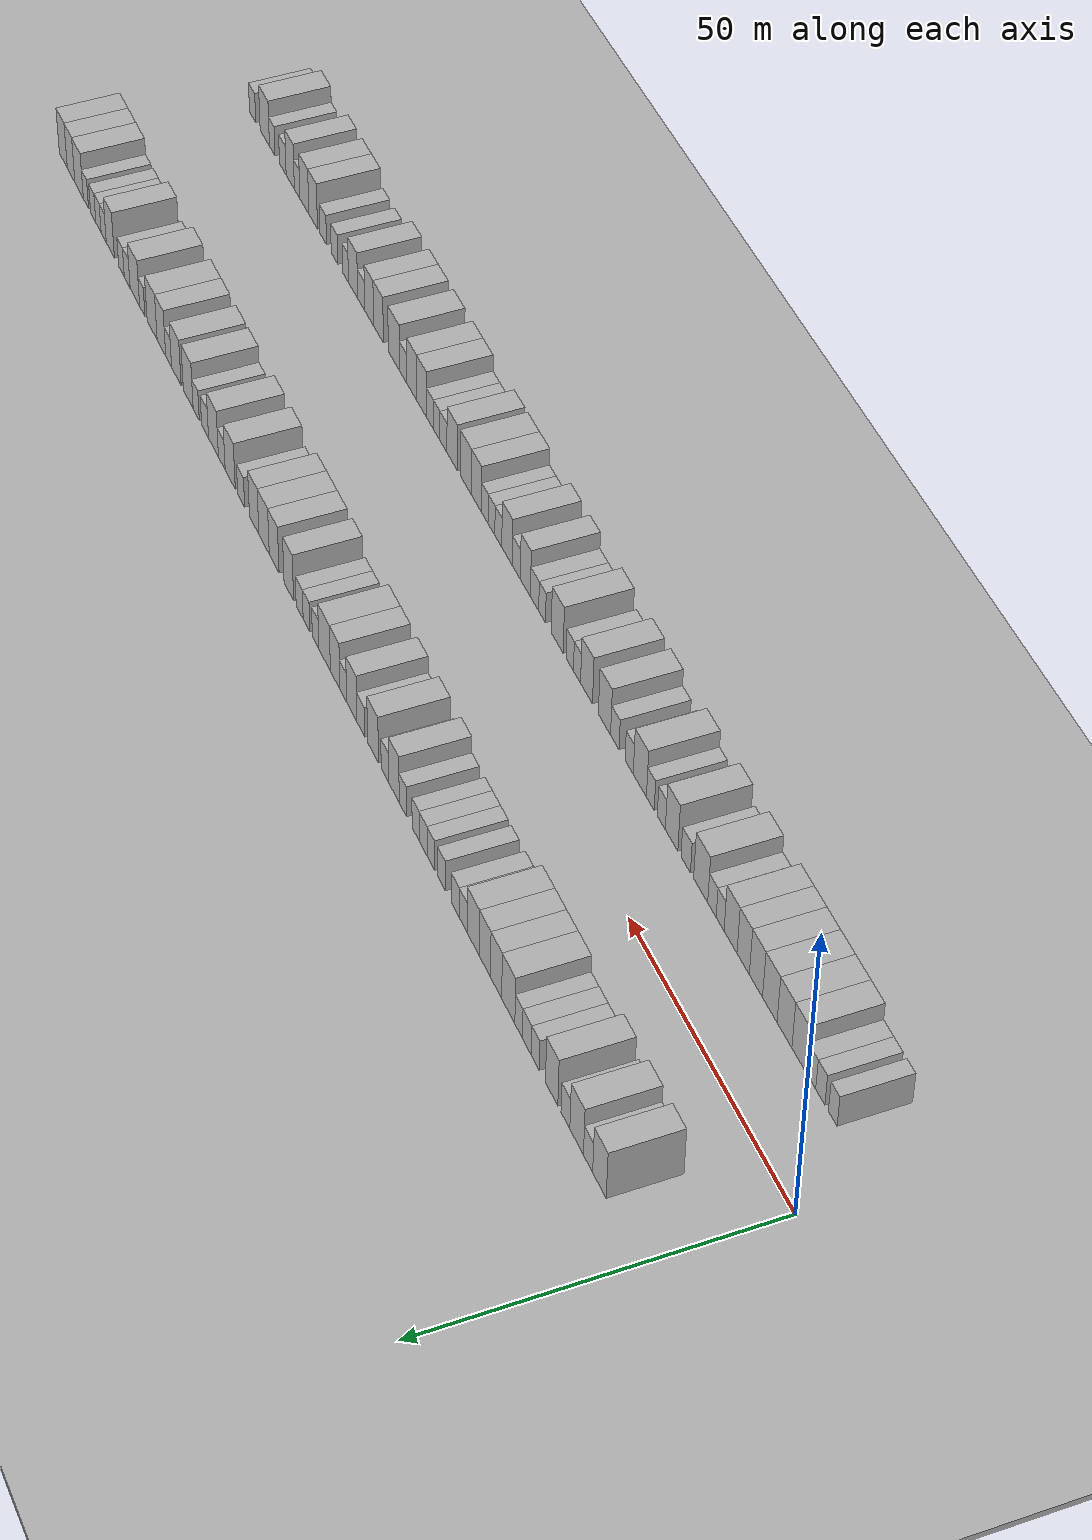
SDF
<?xml version="1.0" encoding="utf-8"?>

<sdf version="1.6">

   <world name="default">

      <gui fullscreen="0">

         <camera name="user_camera">

            <pose>-15 0 4.57585 0 0 0</pose>

            <view_controller>orbit</view_controller>

         </camera>

      </gui>

      <scene>

         <sky>

           <clouds>

             <speed>12</speed>

           </clouds>

         </sky>

         <ambient>0.4 0.4 0.4 1</ambient>

         <background>0.7 0.7 0.7 1</background>

         <shadows>1</shadows>

      </scene>

      <gravity>0 0 -9.8066</gravity>

      <magnetic_field>6e-06 2.3e-05 -4.2e-05</magnetic_field>

      <physics default="0" name="default_physics" type="ode">

         <ode>

            <solver>

               <type>quick</type>

               <iters>10</iters>

               <sor>1.0</sor>

               <use_dynamic_moi_rescaling>0</use_dynamic_moi_rescaling>

            </solver>

            <constraints>

               <cfm>0</cfm>

               <erp>0.2</erp>

               <contact_max_correcting_vel>100</contact_max_correcting_vel>

               <contact_surface_layer>0.001</contact_surface_layer>

            </constraints>

         </ode>

         <max_step_size>0.004</max_step_size>

         <real_time_factor>1</real_time_factor>

         <real_time_update_rate>250</real_time_update_rate>

      </physics>

      <light name="sun" type="directional">

         <cast_shadows>1</cast_shadows>

         <pose>0 0 10 0 0 0</pose>

         <diffuse>0.8 0.8 0.8 1</diffuse>

         <specular>0.2 0.2 0.2 1</specular>

         <attenuation>

            <range>1000</range>

            <constant>0.9</constant>

            <linear>0.01</linear>

            <quadratic>0.001</quadratic>

         </attenuation>

         <direction>-0.5 0.1 -0.9</direction>

      </light>

      <include>

         <name>ground_plane_1</name>

         <uri>model://HANNAS_ground_plane</uri>

         <pose>0 0 0  0 0 0</pose>

      </include>

      <include>

         <name>ground_plane_2</name>

         <uri>model://HANNAS_ground_plane</uri>

         <pose>100 0 0  0 0 0</pose>

      </include>

      <model name="building_1">

         <static>1</static>

         <pose frame="">12.0689 15.0000 0 0.000000 0.000000 1.570796</pose>

         <link name="link">

            <pose frame="">0 0 4.50 0 0 0</pose>

            <collision name="collision">

               <geometry>

                  <box>

                     <size>10.0000 4.1378 9.0000</size>

                  </box>

               </geometry>

               <max_contacts>10</max_contacts>

               <surface>

                  <contact>

                     <ode/>

                  </contact>

                  <bounce/>

                  <friction>

                     <torsional>

                        <ode/>

                     </torsional>

                     <ode/>

                  </friction>

               </surface>

            </collision>

            <visual name="visual">

               <cast_shadows>0</cast_shadows>

               <geometry>

                  <box>

                     <size>10.0000 4.1378 9.0000</size>

                  </box>

               </geometry>

               <material>

                  <script>

                     <uri>model://HANNAS_wall/materials/scripts</uri>

                     <uri>model://HANNAS_wall/materials/textures</uri>

                     <name>vrc/HANNAS_wall</name>

                  </script>

               </material>

            </visual>

            <self_collide>0</self_collide>

            <enable_wind>0</enable_wind>

            <kinematic>0</kinematic>

         </link>

      </model>

      <model name="building_2">

         <static>1</static>

         <pose frame="">15.5600 15.0000 0 0.000000 0.000000 1.570796</pose>

         <link name="link">

            <pose frame="">0 0 3.00 0 0 0</pose>

            <collision name="collision">

               <geometry>

                  <box>

                     <size>10.0000 2.8444 6.0000</size>

                  </box>

               </geometry>

               <max_contacts>10</max_contacts>

               <surface>

                  <contact>

                     <ode/>

                  </contact>

                  <bounce/>

                  <friction>

                     <torsional>

                        <ode/>

                     </torsional>

                     <ode/>

                  </friction>

               </surface>

            </collision>

            <visual name="visual">

               <cast_shadows>0</cast_shadows>

               <geometry>

                  <box>

                     <size>10.0000 2.8444 6.0000</size>

                  </box>

               </geometry>

               <material>

                  <script>

                     <uri>model://HANNAS_wall/materials/scripts</uri>

                     <uri>model://HANNAS_wall/materials/textures</uri>

                     <name>vrc/HANNAS_wall</name>

                  </script>

               </material>

            </visual>

            <self_collide>0</self_collide>

            <enable_wind>0</enable_wind>

            <kinematic>0</kinematic>

         </link>

      </model>

      <model name="building_3">

         <static>1</static>

         <pose frame="">19.1028 15.0000 0 0.000000 0.000000 1.570796</pose>

         <link name="link">

            <pose frame="">0 0 4.50 0 0 0</pose>

            <collision name="collision">

               <geometry>

                  <box>

                     <size>10.0000 4.2411 9.0000</size>

                  </box>

               </geometry>

               <max_contacts>10</max_contacts>

               <surface>

                  <contact>

                     <ode/>

                  </contact>

                  <bounce/>

                  <friction>

                     <torsional>

                        <ode/>

                     </torsional>

                     <ode/>

                  </friction>

               </surface>

            </collision>

            <visual name="visual">

               <cast_shadows>0</cast_shadows>

               <geometry>

                  <box>

                     <size>10.0000 4.2411 9.0000</size>

                  </box>

               </geometry>

               <material>

                  <script>

                     <uri>model://HANNAS_wall/materials/scripts</uri>

                     <uri>model://HANNAS_wall/materials/textures</uri>

                     <name>vrc/HANNAS_wall</name>

                  </script>

               </material>

            </visual>

            <self_collide>0</self_collide>

            <enable_wind>0</enable_wind>

            <kinematic>0</kinematic>

         </link>

      </model>

      <model name="building_4">

         <static>1</static>

         <pose frame="">22.6102 15.0000 0 0.000000 0.000000 1.570796</pose>

         <link name="link">

            <pose frame="">0 0 3.00 0 0 0</pose>

            <collision name="collision">

               <geometry>

                  <box>

                     <size>10.0000 2.7738 6.0000</size>

                  </box>

               </geometry>

               <max_contacts>10</max_contacts>

               <surface>

                  <contact>

                     <ode/>

                  </contact>

                  <bounce/>

                  <friction>

                     <torsional>

                        <ode/>

                     </torsional>

                     <ode/>

                  </friction>

               </surface>

            </collision>

            <visual name="visual">

               <cast_shadows>0</cast_shadows>

               <geometry>

                  <box>

                     <size>10.0000 2.7738 6.0000</size>

                  </box>

               </geometry>

               <material>

                  <script>

                     <uri>model://HANNAS_wall/materials/scripts</uri>

                     <uri>model://HANNAS_wall/materials/textures</uri>

                     <name>vrc/HANNAS_wall</name>

                  </script>

               </material>

            </visual>

            <self_collide>0</self_collide>

            <enable_wind>0</enable_wind>

            <kinematic>0</kinematic>

         </link>

      </model>

      <model name="building_5">

         <static>1</static>

         <pose frame="">26.9591 15.0000 0 0.000000 0.000000 1.570796</pose>

         <link name="link">

            <pose frame="">0 0 4.50 0 0 0</pose>

            <collision name="collision">

               <geometry>

                  <box>

                     <size>10.0000 3.9240 9.0000</size>

                  </box>

               </geometry>

               <max_contacts>10</max_contacts>

               <surface>

                  <contact>

                     <ode/>

                  </contact>

                  <bounce/>

                  <friction>

                     <torsional>

                        <ode/>

                     </torsional>

                     <ode/>

                  </friction>

               </surface>

            </collision>

            <visual name="visual">

               <cast_shadows>0</cast_shadows>

               <geometry>

                  <box>

                     <size>10.0000 3.9240 9.0000</size>

                  </box>

               </geometry>

               <material>

                  <script>

                     <uri>model://HANNAS_wall/materials/scripts</uri>

                     <uri>model://HANNAS_wall/materials/textures</uri>

                     <name>vrc/HANNAS_wall</name>

                  </script>

               </material>

            </visual>

            <self_collide>0</self_collide>

            <enable_wind>0</enable_wind>

            <kinematic>0</kinematic>

         </link>

      </model>

      <model name="building_6">

         <static>1</static>

         <pose frame="">32.1991 15.0000 0 0.000000 0.000000 1.570796</pose>

         <link name="link">

            <pose frame="">0 0 3.00 0 0 0</pose>

            <collision name="collision">

               <geometry>

                  <box>

                     <size>10.0000 2.5560 6.0000</size>

                  </box>

               </geometry>

               <max_contacts>10</max_contacts>

               <surface>

                  <contact>

                     <ode/>

                  </contact>

                  <bounce/>

                  <friction>

                     <torsional>

                        <ode/>

                     </torsional>

                     <ode/>

                  </friction>

               </surface>

            </collision>

            <visual name="visual">

               <cast_shadows>0</cast_shadows>

               <geometry>

                  <box>

                     <size>10.0000 2.5560 6.0000</size>

                  </box>

               </geometry>

               <material>

                  <script>

                     <uri>model://HANNAS_wall/materials/scripts</uri>

                     <uri>model://HANNAS_wall/materials/textures</uri>

                     <name>vrc/HANNAS_wall</name>

                  </script>

               </material>

            </visual>

            <self_collide>0</self_collide>

            <enable_wind>0</enable_wind>

            <kinematic>0</kinematic>

         </link>

      </model>

      <model name="building_7">

         <static>1</static>

         <pose frame="">34.9066 15.0000 0 0.000000 0.000000 1.570796</pose>

         <link name="link">

            <pose frame="">0 0 3.00 0 0 0</pose>

            <collision name="collision">

               <geometry>

                  <box>

                     <size>10.0000 2.8590 6.0000</size>

                  </box>

               </geometry>

               <max_contacts>10</max_contacts>

               <surface>

                  <contact>

                     <ode/>

                  </contact>

                  <bounce/>

                  <friction>

                     <torsional>

                        <ode/>

                     </torsional>

                     <ode/>

                  </friction>

               </surface>

            </collision>

            <visual name="visual">

               <cast_shadows>0</cast_shadows>

               <geometry>

                  <box>

                     <size>10.0000 2.8590 6.0000</size>

                  </box>

               </geometry>

               <material>

                  <script>

                     <uri>model://HANNAS_wall/materials/scripts</uri>

                     <uri>model://HANNAS_wall/materials/textures</uri>

                     <name>vrc/HANNAS_wall</name>

                  </script>

               </material>

            </visual>

            <self_collide>0</self_collide>

            <enable_wind>0</enable_wind>

            <kinematic>0</kinematic>

         </link>

      </model>

      <model name="building_8">

         <static>1</static>

         <pose frame="">37.5727 15.0000 0 0.000000 0.000000 1.570796</pose>

         <link name="link">

            <pose frame="">0 0 3.00 0 0 0</pose>

            <collision name="collision">

               <geometry>

                  <box>

                     <size>10.0000 2.4732 6.0000</size>

                  </box>

               </geometry>

               <max_contacts>10</max_contacts>

               <surface>

                  <contact>

                     <ode/>

                  </contact>

                  <bounce/>

                  <friction>

                     <torsional>

                        <ode/>

                     </torsional>

                     <ode/>

                  </friction>

               </surface>

            </collision>

            <visual name="visual">

               <cast_shadows>0</cast_shadows>

               <geometry>

                  <box>

                     <size>10.0000 2.4732 6.0000</size>

                  </box>

               </geometry>

               <material>

                  <script>

                     <uri>model://HANNAS_wall/materials/scripts</uri>

                     <uri>model://HANNAS_wall/materials/textures</uri>

                     <name>vrc/HANNAS_wall</name>

                  </script>

               </material>

            </visual>

            <self_collide>0</self_collide>

            <enable_wind>0</enable_wind>

            <kinematic>0</kinematic>

         </link>

      </model>

      <model name="building_9">

         <static>1</static>

         <pose frame="">40.9801 15.0000 0 0.000000 0.000000 1.570796</pose>

         <link name="link">

            <pose frame="">0 0 4.50 0 0 0</pose>

            <collision name="collision">

               <geometry>

                  <box>

                     <size>10.0000 4.3416 9.0000</size>

                  </box>

               </geometry>

               <max_contacts>10</max_contacts>

               <surface>

                  <contact>

                     <ode/>

                  </contact>

                  <bounce/>

                  <friction>

                     <torsional>

                        <ode/>

                     </torsional>

                     <ode/>

                  </friction>

               </surface>

            </collision>

            <visual name="visual">

               <cast_shadows>0</cast_shadows>

               <geometry>

                  <box>

                     <size>10.0000 4.3416 9.0000</size>

                  </box>

               </geometry>

               <material>

                  <script>

                     <uri>model://HANNAS_wall/materials/scripts</uri>

                     <uri>model://HANNAS_wall/materials/textures</uri>

                     <name>vrc/HANNAS_wall</name>

                  </script>

               </material>

            </visual>

            <self_collide>0</self_collide>

            <enable_wind>0</enable_wind>

            <kinematic>0</kinematic>

         </link>

      </model>

      <model name="building_10">

         <static>1</static>

         <pose frame="">45.0064 15.0000 0 0.000000 0.000000 1.570796</pose>

         <link name="link">

            <pose frame="">0 0 4.50 0 0 0</pose>

            <collision name="collision">

               <geometry>

                  <box>

                     <size>10.0000 3.7110 9.0000</size>

                  </box>

               </geometry>

               <max_contacts>10</max_contacts>

               <surface>

                  <contact>

                     <ode/>

                  </contact>

                  <bounce/>

                  <friction>

                     <torsional>

                        <ode/>

                     </torsional>

                     <ode/>

                  </friction>

               </surface>

            </collision>

            <visual name="visual">

               <cast_shadows>0</cast_shadows>

               <geometry>

                  <box>

                     <size>10.0000 3.7110 9.0000</size>

                  </box>

               </geometry>

               <material>

                  <script>

                     <uri>model://HANNAS_wall/materials/scripts</uri>

                     <uri>model://HANNAS_wall/materials/textures</uri>

                     <name>vrc/HANNAS_wall</name>

                  </script>

               </material>

            </visual>

            <self_collide>0</self_collide>

            <enable_wind>0</enable_wind>

            <kinematic>0</kinematic>

         </link>

      </model>

      <model name="building_11">

         <static>1</static>

         <pose frame="">48.7529 15.0000 0 0.000000 0.000000 1.570796</pose>

         <link name="link">

            <pose frame="">0 0 4.50 0 0 0</pose>

            <collision name="collision">

               <geometry>

                  <box>

                     <size>10.0000 3.7821 9.0000</size>

                  </box>

               </geometry>

               <max_contacts>10</max_contacts>

               <surface>

                  <contact>

                     <ode/>

                  </contact>

                  <bounce/>

                  <friction>

                     <torsional>

                        <ode/>

                     </torsional>

                     <ode/>

                  </friction>

               </surface>

            </collision>

            <visual name="visual">

               <cast_shadows>0</cast_shadows>

               <geometry>

                  <box>

                     <size>10.0000 3.7821 9.0000</size>

                  </box>

               </geometry>

               <material>

                  <script>

                     <uri>model://HANNAS_wall/materials/scripts</uri>

                     <uri>model://HANNAS_wall/materials/textures</uri>

                     <name>vrc/HANNAS_wall</name>

                  </script>

               </material>

            </visual>

            <self_collide>0</self_collide>

            <enable_wind>0</enable_wind>

            <kinematic>0</kinematic>

         </link>

      </model>

      <model name="building_12">

         <static>1</static>

         <pose frame="">52.6965 15.0000 0 0.000000 0.000000 1.570796</pose>

         <link name="link">

            <pose frame="">0 0 4.50 0 0 0</pose>

            <collision name="collision">

               <geometry>

                  <box>

                     <size>10.0000 4.1051 9.0000</size>

                  </box>

               </geometry>

               <max_contacts>10</max_contacts>

               <surface>

                  <contact>

                     <ode/>

                  </contact>

                  <bounce/>

                  <friction>

                     <torsional>

                        <ode/>

                     </torsional>

                     <ode/>

                  </friction>

               </surface>

            </collision>

            <visual name="visual">

               <cast_shadows>0</cast_shadows>

               <geometry>

                  <box>

                     <size>10.0000 4.1051 9.0000</size>

                  </box>

               </geometry>

               <material>

                  <script>

                     <uri>model://HANNAS_wall/materials/scripts</uri>

                     <uri>model://HANNAS_wall/materials/textures</uri>

                     <name>vrc/HANNAS_wall</name>

                  </script>

               </material>

            </visual>

            <self_collide>0</self_collide>

            <enable_wind>0</enable_wind>

            <kinematic>0</kinematic>

         </link>

      </model>

      <model name="building_13">

         <static>1</static>

         <pose frame="">56.1009 15.0000 0 0.000000 0.000000 1.570796</pose>

         <link name="link">

            <pose frame="">0 0 3.00 0 0 0</pose>

            <collision name="collision">

               <geometry>

                  <box>

                     <size>10.0000 2.7037 6.0000</size>

                  </box>

               </geometry>

               <max_contacts>10</max_contacts>

               <surface>

                  <contact>

                     <ode/>

                  </contact>

                  <bounce/>

                  <friction>

                     <torsional>

                        <ode/>

                     </torsional>

                     <ode/>

                  </friction>

               </surface>

            </collision>

            <visual name="visual">

               <cast_shadows>0</cast_shadows>

               <geometry>

                  <box>

                     <size>10.0000 2.7037 6.0000</size>

                  </box>

               </geometry>

               <material>

                  <script>

                     <uri>model://HANNAS_wall/materials/scripts</uri>

                     <uri>model://HANNAS_wall/materials/textures</uri>

                     <name>vrc/HANNAS_wall</name>

                  </script>

               </material>

            </visual>

            <self_collide>0</self_collide>

            <enable_wind>0</enable_wind>

            <kinematic>0</kinematic>

         </link>

      </model>

      <model name="building_14">

         <static>1</static>

         <pose frame="">58.8511 15.0000 0 0.000000 0.000000 1.570796</pose>

         <link name="link">

            <pose frame="">0 0 3.00 0 0 0</pose>

            <collision name="collision">

               <geometry>

                  <box>

                     <size>10.0000 2.7967 6.0000</size>

                  </box>

               </geometry>

               <max_contacts>10</max_contacts>

               <surface>

                  <contact>

                     <ode/>

                  </contact>

                  <bounce/>

                  <friction>

                     <torsional>

                        <ode/>

                     </torsional>

                     <ode/>

                  </friction>

               </surface>

            </collision>

            <visual name="visual">

               <cast_shadows>0</cast_shadows>

               <geometry>

                  <box>

                     <size>10.0000 2.7967 6.0000</size>

                  </box>

               </geometry>

               <material>

                  <script>

                     <uri>model://HANNAS_wall/materials/scripts</uri>

                     <uri>model://HANNAS_wall/materials/textures</uri>

                     <name>vrc/HANNAS_wall</name>

                  </script>

               </material>

            </visual>

            <self_collide>0</self_collide>

            <enable_wind>0</enable_wind>

            <kinematic>0</kinematic>

         </link>

      </model>

      <model name="building_15">

         <static>1</static>

         <pose frame="">63.5975 15.0000 0 0.000000 0.000000 1.570796</pose>

         <link name="link">

            <pose frame="">0 0 3.00 0 0 0</pose>

            <collision name="collision">

               <geometry>

                  <box>

                     <size>10.0000 2.6962 6.0000</size>

                  </box>

               </geometry>

               <max_contacts>10</max_contacts>

               <surface>

                  <contact>

                     <ode/>

                  </contact>

                  <bounce/>

                  <friction>

                     <torsional>

                        <ode/>

                     </torsional>

                     <ode/>

                  </friction>

               </surface>

            </collision>

            <visual name="visual">

               <cast_shadows>0</cast_shadows>

               <geometry>

                  <box>

                     <size>10.0000 2.6962 6.0000</size>

                  </box>

               </geometry>

               <material>

                  <script>

                     <uri>model://HANNAS_wall/materials/scripts</uri>

                     <uri>model://HANNAS_wall/materials/textures</uri>

                     <name>vrc/HANNAS_wall</name>

                  </script>

               </material>

            </visual>

            <self_collide>0</self_collide>

            <enable_wind>0</enable_wind>

            <kinematic>0</kinematic>

         </link>

      </model>

      <model name="building_16">

         <static>1</static>

         <pose frame="">67.2687 15.0000 0 0.000000 0.000000 1.570796</pose>

         <link name="link">

            <pose frame="">0 0 3.00 0 0 0</pose>

            <collision name="collision">

               <geometry>

                  <box>

                     <size>10.0000 2.6462 6.0000</size>

                  </box>

               </geometry>

               <max_contacts>10</max_contacts>

               <surface>

                  <contact>

                     <ode/>

                  </contact>

                  <bounce/>

                  <friction>

                     <torsional>

                        <ode/>

                     </torsional>

                     <ode/>

                  </friction>

               </surface>

            </collision>

            <visual name="visual">

               <cast_shadows>0</cast_shadows>

               <geometry>

                  <box>

                     <size>10.0000 2.6462 6.0000</size>

                  </box>

               </geometry>

               <material>

                  <script>

                     <uri>model://HANNAS_wall/materials/scripts</uri>

                     <uri>model://HANNAS_wall/materials/textures</uri>

                     <name>vrc/HANNAS_wall</name>

                  </script>

               </material>

            </visual>

            <self_collide>0</self_collide>

            <enable_wind>0</enable_wind>

            <kinematic>0</kinematic>

         </link>

      </model>

      <model name="building_17">

         <static>1</static>

         <pose frame="">69.9906 15.0000 0 0.000000 0.000000 1.570796</pose>

         <link name="link">

            <pose frame="">0 0 3.00 0 0 0</pose>

            <collision name="collision">

               <geometry>

                  <box>

                     <size>10.0000 2.7976 6.0000</size>

                  </box>

               </geometry>

               <max_contacts>10</max_contacts>

               <surface>

                  <contact>

                     <ode/>

                  </contact>

                  <bounce/>

                  <friction>

                     <torsional>

                        <ode/>

                     </torsional>

                     <ode/>

                  </friction>

               </surface>

            </collision>

            <visual name="visual">

               <cast_shadows>0</cast_shadows>

               <geometry>

                  <box>

                     <size>10.0000 2.7976 6.0000</size>

                  </box>

               </geometry>

               <material>

                  <script>

                     <uri>model://HANNAS_wall/materials/scripts</uri>

                     <uri>model://HANNAS_wall/materials/textures</uri>

                     <name>vrc/HANNAS_wall</name>

                  </script>

               </material>

            </visual>

            <self_collide>0</self_collide>

            <enable_wind>0</enable_wind>

            <kinematic>0</kinematic>

         </link>

      </model>

      <model name="building_18">

         <static>1</static>

         <pose frame="">72.6465 15.0000 0 0.000000 0.000000 1.570796</pose>

         <link name="link">

            <pose frame="">0 0 3.00 0 0 0</pose>

            <collision name="collision">

               <geometry>

                  <box>

                     <size>10.0000 2.5141 6.0000</size>

                  </box>

               </geometry>

               <max_contacts>10</max_contacts>

               <surface>

                  <contact>

                     <ode/>

                  </contact>

                  <bounce/>

                  <friction>

                     <torsional>

                        <ode/>

                     </torsional>

                     <ode/>

                  </friction>

               </surface>

            </collision>

            <visual name="visual">

               <cast_shadows>0</cast_shadows>

               <geometry>

                  <box>

                     <size>10.0000 2.5141 6.0000</size>

                  </box>

               </geometry>

               <material>

                  <script>

                     <uri>model://HANNAS_wall/materials/scripts</uri>

                     <uri>model://HANNAS_wall/materials/textures</uri>

                     <name>vrc/HANNAS_wall</name>

                  </script>

               </material>

            </visual>

            <self_collide>0</self_collide>

            <enable_wind>0</enable_wind>

            <kinematic>0</kinematic>

         </link>

      </model>

      <model name="building_19">

         <static>1</static>

         <pose frame="">77.2143 15.0000 0 0.000000 0.000000 1.570796</pose>

         <link name="link">

            <pose frame="">0 0 3.00 0 0 0</pose>

            <collision name="collision">

               <geometry>

                  <box>

                     <size>10.0000 2.6215 6.0000</size>

                  </box>

               </geometry>

               <max_contacts>10</max_contacts>

               <surface>

                  <contact>

                     <ode/>

                  </contact>

                  <bounce/>

                  <friction>

                     <torsional>

                        <ode/>

                     </torsional>

                     <ode/>

                  </friction>

               </surface>

            </collision>

            <visual name="visual">

               <cast_shadows>0</cast_shadows>

               <geometry>

                  <box>

                     <size>10.0000 2.6215 6.0000</size>

                  </box>

               </geometry>

               <material>

                  <script>

                     <uri>model://HANNAS_wall/materials/scripts</uri>

                     <uri>model://HANNAS_wall/materials/textures</uri>

                     <name>vrc/HANNAS_wall</name>

                  </script>

               </material>

            </visual>

            <self_collide>0</self_collide>

            <enable_wind>0</enable_wind>

            <kinematic>0</kinematic>

         </link>

      </model>

      <model name="building_20">

         <static>1</static>

         <pose frame="">80.3716 15.0000 0 0.000000 0.000000 1.570796</pose>

         <link name="link">

            <pose frame="">0 0 4.50 0 0 0</pose>

            <collision name="collision">

               <geometry>

                  <box>

                     <size>10.0000 3.6931 9.0000</size>

                  </box>

               </geometry>

               <max_contacts>10</max_contacts>

               <surface>

                  <contact>

                     <ode/>

                  </contact>

                  <bounce/>

                  <friction>

                     <torsional>

                        <ode/>

                     </torsional>

                     <ode/>

                  </friction>

               </surface>

            </collision>

            <visual name="visual">

               <cast_shadows>0</cast_shadows>

               <geometry>

                  <box>

                     <size>10.0000 3.6931 9.0000</size>

                  </box>

               </geometry>

               <material>

                  <script>

                     <uri>model://HANNAS_wall/materials/scripts</uri>

                     <uri>model://HANNAS_wall/materials/textures</uri>

                     <name>vrc/HANNAS_wall</name>

                  </script>

               </material>

            </visual>

            <self_collide>0</self_collide>

            <enable_wind>0</enable_wind>

            <kinematic>0</kinematic>

         </link>

      </model>

      <model name="building_21">

         <static>1</static>

         <pose frame="">83.6435 15.0000 0 0.000000 0.000000 1.570796</pose>

         <link name="link">

            <pose frame="">0 0 3.00 0 0 0</pose>

            <collision name="collision">

               <geometry>

                  <box>

                     <size>10.0000 2.8508 6.0000</size>

                  </box>

               </geometry>

               <max_contacts>10</max_contacts>

               <surface>

                  <contact>

                     <ode/>

                  </contact>

                  <bounce/>

                  <friction>

                     <torsional>

                        <ode/>

                     </torsional>

                     <ode/>

                  </friction>

               </surface>

            </collision>

            <visual name="visual">

               <cast_shadows>0</cast_shadows>

               <geometry>

                  <box>

                     <size>10.0000 2.8508 6.0000</size>

                  </box>

               </geometry>

               <material>

                  <script>

                     <uri>model://HANNAS_wall/materials/scripts</uri>

                     <uri>model://HANNAS_wall/materials/textures</uri>

                     <name>vrc/HANNAS_wall</name>

                  </script>

               </material>

            </visual>

            <self_collide>0</self_collide>

            <enable_wind>0</enable_wind>

            <kinematic>0</kinematic>

         </link>

      </model>

      <model name="building_22">

         <static>1</static>

         <pose frame="">88.0802 15.0000 0 0.000000 0.000000 1.570796</pose>

         <link name="link">

            <pose frame="">0 0 4.50 0 0 0</pose>

            <collision name="collision">

               <geometry>

                  <box>

                     <size>10.0000 4.0225 9.0000</size>

                  </box>

               </geometry>

               <max_contacts>10</max_contacts>

               <surface>

                  <contact>

                     <ode/>

                  </contact>

                  <bounce/>

                  <friction>

                     <torsional>

                        <ode/>

                     </torsional>

                     <ode/>

                  </friction>

               </surface>

            </collision>

            <visual name="visual">

               <cast_shadows>0</cast_shadows>

               <geometry>

                  <box>

                     <size>10.0000 4.0225 9.0000</size>

                  </box>

               </geometry>

               <material>

                  <script>

                     <uri>model://HANNAS_wall/materials/scripts</uri>

                     <uri>model://HANNAS_wall/materials/textures</uri>

                     <name>vrc/HANNAS_wall</name>

                  </script>

               </material>

            </visual>

            <self_collide>0</self_collide>

            <enable_wind>0</enable_wind>

            <kinematic>0</kinematic>

         </link>

      </model>

      <model name="building_23">

         <static>1</static>

         <pose frame="">92.5674 15.0000 0 0.000000 0.000000 1.570796</pose>

         <link name="link">

            <pose frame="">0 0 3.00 0 0 0</pose>

            <collision name="collision">

               <geometry>

                  <box>

                     <size>10.0000 2.9518 6.0000</size>

                  </box>

               </geometry>

               <max_contacts>10</max_contacts>

               <surface>

                  <contact>

                     <ode/>

                  </contact>

                  <bounce/>

                  <friction>

                     <torsional>

                        <ode/>

                     </torsional>

                     <ode/>

                  </friction>

               </surface>

            </collision>

            <visual name="visual">

               <cast_shadows>0</cast_shadows>

               <geometry>

                  <box>

                     <size>10.0000 2.9518 6.0000</size>

                  </box>

               </geometry>

               <material>

                  <script>

                     <uri>model://HANNAS_wall/materials/scripts</uri>

                     <uri>model://HANNAS_wall/materials/textures</uri>

                     <name>vrc/HANNAS_wall</name>

                  </script>

               </material>

            </visual>

            <self_collide>0</self_collide>

            <enable_wind>0</enable_wind>

            <kinematic>0</kinematic>

         </link>

      </model>

      <model name="building_24">

         <static>1</static>

         <pose frame="">95.9662 15.0000 0 0.000000 0.000000 1.570796</pose>

         <link name="link">

            <pose frame="">0 0 4.50 0 0 0</pose>

            <collision name="collision">

               <geometry>

                  <box>

                     <size>10.0000 3.8458 9.0000</size>

                  </box>

               </geometry>

               <max_contacts>10</max_contacts>

               <surface>

                  <contact>

                     <ode/>

                  </contact>

                  <bounce/>

                  <friction>

                     <torsional>

                        <ode/>

                     </torsional>

                     <ode/>

                  </friction>

               </surface>

            </collision>

            <visual name="visual">

               <cast_shadows>0</cast_shadows>

               <geometry>

                  <box>

                     <size>10.0000 3.8458 9.0000</size>

                  </box>

               </geometry>

               <material>

                  <script>

                     <uri>model://HANNAS_wall/materials/scripts</uri>

                     <uri>model://HANNAS_wall/materials/textures</uri>

                     <name>vrc/HANNAS_wall</name>

                  </script>

               </material>

            </visual>

            <self_collide>0</self_collide>

            <enable_wind>0</enable_wind>

            <kinematic>0</kinematic>

         </link>

      </model>

      <model name="building_25">

         <static>1</static>

         <pose frame="">99.1635 15.0000 0 0.000000 0.000000 1.570796</pose>

         <link name="link">

            <pose frame="">0 0 3.00 0 0 0</pose>

            <collision name="collision">

               <geometry>

                  <box>

                     <size>10.0000 2.5488 6.0000</size>

                  </box>

               </geometry>

               <max_contacts>10</max_contacts>

               <surface>

                  <contact>

                     <ode/>

                  </contact>

                  <bounce/>

                  <friction>

                     <torsional>

                        <ode/>

                     </torsional>

                     <ode/>

                  </friction>

               </surface>

            </collision>

            <visual name="visual">

               <cast_shadows>0</cast_shadows>

               <geometry>

                  <box>

                     <size>10.0000 2.5488 6.0000</size>

                  </box>

               </geometry>

               <material>

                  <script>

                     <uri>model://HANNAS_wall/materials/scripts</uri>

                     <uri>model://HANNAS_wall/materials/textures</uri>

                     <name>vrc/HANNAS_wall</name>

                  </script>

               </material>

            </visual>

            <self_collide>0</self_collide>

            <enable_wind>0</enable_wind>

            <kinematic>0</kinematic>

         </link>

      </model>

      <model name="building_26">

         <static>1</static>

         <pose frame="">102.2581 15.0000 0 0.000000 0.000000 1.570796</pose>

         <link name="link">

            <pose frame="">0 0 4.50 0 0 0</pose>

            <collision name="collision">

               <geometry>

                  <box>

                     <size>10.0000 3.6404 9.0000</size>

                  </box>

               </geometry>

               <max_contacts>10</max_contacts>

               <surface>

                  <contact>

                     <ode/>

                  </contact>

                  <bounce/>

                  <friction>

                     <torsional>

                        <ode/>

                     </torsional>

                     <ode/>

                  </friction>

               </surface>

            </collision>

            <visual name="visual">

               <cast_shadows>0</cast_shadows>

               <geometry>

                  <box>

                     <size>10.0000 3.6404 9.0000</size>

                  </box>

               </geometry>

               <material>

                  <script>

                     <uri>model://HANNAS_wall/materials/scripts</uri>

                     <uri>model://HANNAS_wall/materials/textures</uri>

                     <name>vrc/HANNAS_wall</name>

                  </script>

               </material>

            </visual>

            <self_collide>0</self_collide>

            <enable_wind>0</enable_wind>

            <kinematic>0</kinematic>

         </link>

      </model>

      <model name="building_27">

         <static>1</static>

         <pose frame="">106.2851 15.0000 0 0.000000 0.000000 1.570796</pose>

         <link name="link">

            <pose frame="">0 0 4.50 0 0 0</pose>

            <collision name="collision">

               <geometry>

                  <box>

                     <size>10.0000 4.4137 9.0000</size>

                  </box>

               </geometry>

               <max_contacts>10</max_contacts>

               <surface>

                  <contact>

                     <ode/>

                  </contact>

                  <bounce/>

                  <friction>

                     <torsional>

                        <ode/>

                     </torsional>

                     <ode/>

                  </friction>

               </surface>

            </collision>

            <visual name="visual">

               <cast_shadows>0</cast_shadows>

               <geometry>

                  <box>

                     <size>10.0000 4.4137 9.0000</size>

                  </box>

               </geometry>

               <material>

                  <script>

                     <uri>model://HANNAS_wall/materials/scripts</uri>

                     <uri>model://HANNAS_wall/materials/textures</uri>

                     <name>vrc/HANNAS_wall</name>

                  </script>

               </material>

            </visual>

            <self_collide>0</self_collide>

            <enable_wind>0</enable_wind>

            <kinematic>0</kinematic>

         </link>

      </model>

      <model name="building_28">

         <static>1</static>

         <pose frame="">109.7603 15.0000 0 0.000000 0.000000 1.570796</pose>

         <link name="link">

            <pose frame="">0 0 3.00 0 0 0</pose>

            <collision name="collision">

               <geometry>

                  <box>

                     <size>10.0000 2.5368 6.0000</size>

                  </box>

               </geometry>

               <max_contacts>10</max_contacts>

               <surface>

                  <contact>

                     <ode/>

                  </contact>

                  <bounce/>

                  <friction>

                     <torsional>

                        <ode/>

                     </torsional>

                     <ode/>

                  </friction>

               </surface>

            </collision>

            <visual name="visual">

               <cast_shadows>0</cast_shadows>

               <geometry>

                  <box>

                     <size>10.0000 2.5368 6.0000</size>

                  </box>

               </geometry>

               <material>

                  <script>

                     <uri>model://HANNAS_wall/materials/scripts</uri>

                     <uri>model://HANNAS_wall/materials/textures</uri>

                     <name>vrc/HANNAS_wall</name>

                  </script>

               </material>

            </visual>

            <self_collide>0</self_collide>

            <enable_wind>0</enable_wind>

            <kinematic>0</kinematic>

         </link>

      </model>

      <model name="building_29">

         <static>1</static>

         <pose frame="">113.3267 15.0000 0 0.000000 0.000000 1.570796</pose>

         <link name="link">

            <pose frame="">0 0 3.00 0 0 0</pose>

            <collision name="collision">

               <geometry>

                  <box>

                     <size>10.0000 2.5958 6.0000</size>

                  </box>

               </geometry>

               <max_contacts>10</max_contacts>

               <surface>

                  <contact>

                     <ode/>

                  </contact>

                  <bounce/>

                  <friction>

                     <torsional>

                        <ode/>

                     </torsional>

                     <ode/>

                  </friction>

               </surface>

            </collision>

            <visual name="visual">

               <cast_shadows>0</cast_shadows>

               <geometry>

                  <box>

                     <size>10.0000 2.5958 6.0000</size>

                  </box>

               </geometry>

               <material>

                  <script>

                     <uri>model://HANNAS_wall/materials/scripts</uri>

                     <uri>model://HANNAS_wall/materials/textures</uri>

                     <name>vrc/HANNAS_wall</name>

                  </script>

               </material>

            </visual>

            <self_collide>0</self_collide>

            <enable_wind>0</enable_wind>

            <kinematic>0</kinematic>

         </link>

      </model>

      <model name="building_30">

         <static>1</static>

         <pose frame="">116.0006 15.0000 0 0.000000 0.000000 1.570796</pose>

         <link name="link">

            <pose frame="">0 0 3.00 0 0 0</pose>

            <collision name="collision">

               <geometry>

                  <box>

                     <size>10.0000 2.7520 6.0000</size>

                  </box>

               </geometry>

               <max_contacts>10</max_contacts>

               <surface>

                  <contact>

                     <ode/>

                  </contact>

                  <bounce/>

                  <friction>

                     <torsional>

                        <ode/>

                     </torsional>

                     <ode/>

                  </friction>

               </surface>

            </collision>

            <visual name="visual">

               <cast_shadows>0</cast_shadows>

               <geometry>

                  <box>

                     <size>10.0000 2.7520 6.0000</size>

                  </box>

               </geometry>

               <material>

                  <script>

                     <uri>model://HANNAS_wall/materials/scripts</uri>

                     <uri>model://HANNAS_wall/materials/textures</uri>

                     <name>vrc/HANNAS_wall</name>

                  </script>

               </material>

            </visual>

            <self_collide>0</self_collide>

            <enable_wind>0</enable_wind>

            <kinematic>0</kinematic>

         </link>

      </model>

      <model name="building_31">

         <static>1</static>

         <pose frame="">120.2804 15.0000 0 0.000000 0.000000 1.570796</pose>

         <link name="link">

            <pose frame="">0 0 4.50 0 0 0</pose>

            <collision name="collision">

               <geometry>

                  <box>

                     <size>10.0000 3.8077 9.0000</size>

                  </box>

               </geometry>

               <max_contacts>10</max_contacts>

               <surface>

                  <contact>

                     <ode/>

                  </contact>

                  <bounce/>

                  <friction>

                     <torsional>

                        <ode/>

                     </torsional>

                     <ode/>

                  </friction>

               </surface>

            </collision>

            <visual name="visual">

               <cast_shadows>0</cast_shadows>

               <geometry>

                  <box>

                     <size>10.0000 3.8077 9.0000</size>

                  </box>

               </geometry>

               <material>

                  <script>

                     <uri>model://HANNAS_wall/materials/scripts</uri>

                     <uri>model://HANNAS_wall/materials/textures</uri>

                     <name>vrc/HANNAS_wall</name>

                  </script>

               </material>

            </visual>

            <self_collide>0</self_collide>

            <enable_wind>0</enable_wind>

            <kinematic>0</kinematic>

         </link>

      </model>

      <model name="building_32">

         <static>1</static>

         <pose frame="">126.1542 15.0000 0 0.000000 0.000000 1.570796</pose>

         <link name="link">

            <pose frame="">0 0 4.50 0 0 0</pose>

            <collision name="collision">

               <geometry>

                  <box>

                     <size>10.0000 3.9397 9.0000</size>

                  </box>

               </geometry>

               <max_contacts>10</max_contacts>

               <surface>

                  <contact>

                     <ode/>

                  </contact>

                  <bounce/>

                  <friction>

                     <torsional>

                        <ode/>

                     </torsional>

                     <ode/>

                  </friction>

               </surface>

            </collision>

            <visual name="visual">

               <cast_shadows>0</cast_shadows>

               <geometry>

                  <box>

                     <size>10.0000 3.9397 9.0000</size>

                  </box>

               </geometry>

               <material>

                  <script>

                     <uri>model://HANNAS_wall/materials/scripts</uri>

                     <uri>model://HANNAS_wall/materials/textures</uri>

                     <name>vrc/HANNAS_wall</name>

                  </script>

               </material>

            </visual>

            <self_collide>0</self_collide>

            <enable_wind>0</enable_wind>

            <kinematic>0</kinematic>

         </link>

      </model>

      <model name="building_33">

         <static>1</static>

         <pose frame="">130.2297 15.0000 0 0.000000 0.000000 1.570796</pose>

         <link name="link">

            <pose frame="">0 0 4.50 0 0 0</pose>

            <collision name="collision">

               <geometry>

                  <box>

                     <size>10.0000 4.2113 9.0000</size>

                  </box>

               </geometry>

               <max_contacts>10</max_contacts>

               <surface>

                  <contact>

                     <ode/>

                  </contact>

                  <bounce/>

                  <friction>

                     <torsional>

                        <ode/>

                     </torsional>

                     <ode/>

                  </friction>

               </surface>

            </collision>

            <visual name="visual">

               <cast_shadows>0</cast_shadows>

               <geometry>

                  <box>

                     <size>10.0000 4.2113 9.0000</size>

                  </box>

               </geometry>

               <material>

                  <script>

                     <uri>model://HANNAS_wall/materials/scripts</uri>

                     <uri>model://HANNAS_wall/materials/textures</uri>

                     <name>vrc/HANNAS_wall</name>

                  </script>

               </material>

            </visual>

            <self_collide>0</self_collide>

            <enable_wind>0</enable_wind>

            <kinematic>0</kinematic>

         </link>

      </model>

      <model name="building_34">

         <static>1</static>

         <pose frame="">134.2596 15.0000 0 0.000000 0.000000 1.570796</pose>

         <link name="link">

            <pose frame="">0 0 4.50 0 0 0</pose>

            <collision name="collision">

               <geometry>

                  <box>

                     <size>10.0000 3.8485 9.0000</size>

                  </box>

               </geometry>

               <max_contacts>10</max_contacts>

               <surface>

                  <contact>

                     <ode/>

                  </contact>

                  <bounce/>

                  <friction>

                     <torsional>

                        <ode/>

                     </torsional>

                     <ode/>

                  </friction>

               </surface>

            </collision>

            <visual name="visual">

               <cast_shadows>0</cast_shadows>

               <geometry>

                  <box>

                     <size>10.0000 3.8485 9.0000</size>

                  </box>

               </geometry>

               <material>

                  <script>

                     <uri>model://HANNAS_wall/materials/scripts</uri>

                     <uri>model://HANNAS_wall/materials/textures</uri>

                     <name>vrc/HANNAS_wall</name>

                  </script>

               </material>

            </visual>

            <self_collide>0</self_collide>

            <enable_wind>0</enable_wind>

            <kinematic>0</kinematic>

         </link>

      </model>

      <model name="building_35">

         <static>1</static>

         <pose frame="">139.6347 15.0000 0 0.000000 0.000000 1.570796</pose>

         <link name="link">

            <pose frame="">0 0 3.00 0 0 0</pose>

            <collision name="collision">

               <geometry>

                  <box>

                     <size>10.0000 2.9016 6.0000</size>

                  </box>

               </geometry>

               <max_contacts>10</max_contacts>

               <surface>

                  <contact>

                     <ode/>

                  </contact>

                  <bounce/>

                  <friction>

                     <torsional>

                        <ode/>

                     </torsional>

                     <ode/>

                  </friction>

               </surface>

            </collision>

            <visual name="visual">

               <cast_shadows>0</cast_shadows>

               <geometry>

                  <box>

                     <size>10.0000 2.9016 6.0000</size>

                  </box>

               </geometry>

               <material>

                  <script>

                     <uri>model://HANNAS_wall/materials/scripts</uri>

                     <uri>model://HANNAS_wall/materials/textures</uri>

                     <name>vrc/HANNAS_wall</name>

                  </script>

               </material>

            </visual>

            <self_collide>0</self_collide>

            <enable_wind>0</enable_wind>

            <kinematic>0</kinematic>

         </link>

      </model>

      <model name="building_36">

         <static>1</static>

         <pose frame="">144.2004 15.0000 0 0.000000 0.000000 1.570796</pose>

         <link name="link">

            <pose frame="">0 0 4.50 0 0 0</pose>

            <collision name="collision">

               <geometry>

                  <box>

                     <size>10.0000 4.2298 9.0000</size>

                  </box>

               </geometry>

               <max_contacts>10</max_contacts>

               <surface>

                  <contact>

                     <ode/>

                  </contact>

                  <bounce/>

                  <friction>

                     <torsional>

                        <ode/>

                     </torsional>

                     <ode/>

                  </friction>

               </surface>

            </collision>

            <visual name="visual">

               <cast_shadows>0</cast_shadows>

               <geometry>

                  <box>

                     <size>10.0000 4.2298 9.0000</size>

                  </box>

               </geometry>

               <material>

                  <script>

                     <uri>model://HANNAS_wall/materials/scripts</uri>

                     <uri>model://HANNAS_wall/materials/textures</uri>

                     <name>vrc/HANNAS_wall</name>

                  </script>

               </material>

            </visual>

            <self_collide>0</self_collide>

            <enable_wind>0</enable_wind>

            <kinematic>0</kinematic>

         </link>

      </model>

      <model name="building_37">

         <static>1</static>

         <pose frame="">147.7412 15.0000 0 0.000000 0.000000 1.570796</pose>

         <link name="link">

            <pose frame="">0 0 3.00 0 0 0</pose>

            <collision name="collision">

               <geometry>

                  <box>

                     <size>10.0000 2.8519 6.0000</size>

                  </box>

               </geometry>

               <max_contacts>10</max_contacts>

               <surface>

                  <contact>

                     <ode/>

                  </contact>

                  <bounce/>

                  <friction>

                     <torsional>

                        <ode/>

                     </torsional>

                     <ode/>

                  </friction>

               </surface>

            </collision>

            <visual name="visual">

               <cast_shadows>0</cast_shadows>

               <geometry>

                  <box>

                     <size>10.0000 2.8519 6.0000</size>

                  </box>

               </geometry>

               <material>

                  <script>

                     <uri>model://HANNAS_wall/materials/scripts</uri>

                     <uri>model://HANNAS_wall/materials/textures</uri>

                     <name>vrc/HANNAS_wall</name>

                  </script>

               </material>

            </visual>

            <self_collide>0</self_collide>

            <enable_wind>0</enable_wind>

            <kinematic>0</kinematic>

         </link>

      </model>

      <model name="building_38">

         <static>1</static>

         <pose frame="">151.2683 15.0000 0 0.000000 0.000000 1.570796</pose>

         <link name="link">

            <pose frame="">0 0 4.50 0 0 0</pose>

            <collision name="collision">

               <geometry>

                  <box>

                     <size>10.0000 4.2023 9.0000</size>

                  </box>

               </geometry>

               <max_contacts>10</max_contacts>

               <surface>

                  <contact>

                     <ode/>

                  </contact>

                  <bounce/>

                  <friction>

                     <torsional>

                        <ode/>

                     </torsional>

                     <ode/>

                  </friction>

               </surface>

            </collision>

            <visual name="visual">

               <cast_shadows>0</cast_shadows>

               <geometry>

                  <box>

                     <size>10.0000 4.2023 9.0000</size>

                  </box>

               </geometry>

               <material>

                  <script>

                     <uri>model://HANNAS_wall/materials/scripts</uri>

                     <uri>model://HANNAS_wall/materials/textures</uri>

                     <name>vrc/HANNAS_wall</name>

                  </script>

               </material>

            </visual>

            <self_collide>0</self_collide>

            <enable_wind>0</enable_wind>

            <kinematic>0</kinematic>

         </link>

      </model>

      <model name="building_39">

         <static>1</static>

         <pose frame="">154.8601 15.0000 0 0.000000 0.000000 1.570796</pose>

         <link name="link">

            <pose frame="">0 0 3.00 0 0 0</pose>

            <collision name="collision">

               <geometry>

                  <box>

                     <size>10.0000 2.9813 6.0000</size>

                  </box>

               </geometry>

               <max_contacts>10</max_contacts>

               <surface>

                  <contact>

                     <ode/>

                  </contact>

                  <bounce/>

                  <friction>

                     <torsional>

                        <ode/>

                     </torsional>

                     <ode/>

                  </friction>

               </surface>

            </collision>

            <visual name="visual">

               <cast_shadows>0</cast_shadows>

               <geometry>

                  <box>

                     <size>10.0000 2.9813 6.0000</size>

                  </box>

               </geometry>

               <material>

                  <script>

                     <uri>model://HANNAS_wall/materials/scripts</uri>

                     <uri>model://HANNAS_wall/materials/textures</uri>

                     <name>vrc/HANNAS_wall</name>

                  </script>

               </material>

            </visual>

            <self_collide>0</self_collide>

            <enable_wind>0</enable_wind>

            <kinematic>0</kinematic>

         </link>

      </model>

      <model name="building_40">

         <static>1</static>

         <pose frame="">158.6745 15.0000 0 0.000000 0.000000 1.570796</pose>

         <link name="link">

            <pose frame="">0 0 3.00 0 0 0</pose>

            <collision name="collision">

               <geometry>

                  <box>

                     <size>10.0000 2.6474 6.0000</size>

                  </box>

               </geometry>

               <max_contacts>10</max_contacts>

               <surface>

                  <contact>

                     <ode/>

                  </contact>

                  <bounce/>

                  <friction>

                     <torsional>

                        <ode/>

                     </torsional>

                     <ode/>

                  </friction>

               </surface>

            </collision>

            <visual name="visual">

               <cast_shadows>0</cast_shadows>

               <geometry>

                  <box>

                     <size>10.0000 2.6474 6.0000</size>

                  </box>

               </geometry>

               <material>

                  <script>

                     <uri>model://HANNAS_wall/materials/scripts</uri>

                     <uri>model://HANNAS_wall/materials/textures</uri>

                     <name>vrc/HANNAS_wall</name>

                  </script>

               </material>

            </visual>

            <self_collide>0</self_collide>

            <enable_wind>0</enable_wind>

            <kinematic>0</kinematic>

         </link>

      </model>

      <model name="building_41">

         <static>1</static>

         <pose frame="">162.1215 15.0000 0 0.000000 0.000000 1.570796</pose>

         <link name="link">

            <pose frame="">0 0 4.50 0 0 0</pose>

            <collision name="collision">

               <geometry>

                  <box>

                     <size>10.0000 4.2467 9.0000</size>

                  </box>

               </geometry>

               <max_contacts>10</max_contacts>

               <surface>

                  <contact>

                     <ode/>

                  </contact>

                  <bounce/>

                  <friction>

                     <torsional>

                        <ode/>

                     </torsional>

                     <ode/>

                  </friction>

               </surface>

            </collision>

            <visual name="visual">

               <cast_shadows>0</cast_shadows>

               <geometry>

                  <box>

                     <size>10.0000 4.2467 9.0000</size>

                  </box>

               </geometry>

               <material>

                  <script>

                     <uri>model://HANNAS_wall/materials/scripts</uri>

                     <uri>model://HANNAS_wall/materials/textures</uri>

                     <name>vrc/HANNAS_wall</name>

                  </script>

               </material>

            </visual>

            <self_collide>0</self_collide>

            <enable_wind>0</enable_wind>

            <kinematic>0</kinematic>

         </link>

      </model>

      <model name="building_42">

         <static>1</static>

         <pose frame="">167.3455 15.0000 0 0.000000 0.000000 1.570796</pose>

         <link name="link">

            <pose frame="">0 0 4.50 0 0 0</pose>

            <collision name="collision">

               <geometry>

                  <box>

                     <size>10.0000 4.2012 9.0000</size>

                  </box>

               </geometry>

               <max_contacts>10</max_contacts>

               <surface>

                  <contact>

                     <ode/>

                  </contact>

                  <bounce/>

                  <friction>

                     <torsional>

                        <ode/>

                     </torsional>

                     <ode/>

                  </friction>

               </surface>

            </collision>

            <visual name="visual">

               <cast_shadows>0</cast_shadows>

               <geometry>

                  <box>

                     <size>10.0000 4.2012 9.0000</size>

                  </box>

               </geometry>

               <material>

                  <script>

                     <uri>model://HANNAS_wall/materials/scripts</uri>

                     <uri>model://HANNAS_wall/materials/textures</uri>

                     <name>vrc/HANNAS_wall</name>

                  </script>

               </material>

            </visual>

            <self_collide>0</self_collide>

            <enable_wind>0</enable_wind>

            <kinematic>0</kinematic>

         </link>

      </model>

      <model name="building_43">

         <static>1</static>

         <pose frame="">170.7555 15.0000 0 0.000000 0.000000 1.570796</pose>

         <link name="link">

            <pose frame="">0 0 3.00 0 0 0</pose>

            <collision name="collision">

               <geometry>

                  <box>

                     <size>10.0000 2.6189 6.0000</size>

                  </box>

               </geometry>

               <max_contacts>10</max_contacts>

               <surface>

                  <contact>

                     <ode/>

                  </contact>

                  <bounce/>

                  <friction>

                     <torsional>

                        <ode/>

                     </torsional>

                     <ode/>

                  </friction>

               </surface>

            </collision>

            <visual name="visual">

               <cast_shadows>0</cast_shadows>

               <geometry>

                  <box>

                     <size>10.0000 2.6189 6.0000</size>

                  </box>

               </geometry>

               <material>

                  <script>

                     <uri>model://HANNAS_wall/materials/scripts</uri>

                     <uri>model://HANNAS_wall/materials/textures</uri>

                     <name>vrc/HANNAS_wall</name>

                  </script>

               </material>

            </visual>

            <self_collide>0</self_collide>

            <enable_wind>0</enable_wind>

            <kinematic>0</kinematic>

         </link>

      </model>

      <model name="building_44">

         <static>1</static>

         <pose frame="">173.9769 15.0000 0 0.000000 0.000000 1.570796</pose>

         <link name="link">

            <pose frame="">0 0 4.50 0 0 0</pose>

            <collision name="collision">

               <geometry>

                  <box>

                     <size>10.0000 3.8240 9.0000</size>

                  </box>

               </geometry>

               <max_contacts>10</max_contacts>

               <surface>

                  <contact>

                     <ode/>

                  </contact>

                  <bounce/>

                  <friction>

                     <torsional>

                        <ode/>

                     </torsional>

                     <ode/>

                  </friction>

               </surface>

            </collision>

            <visual name="visual">

               <cast_shadows>0</cast_shadows>

               <geometry>

                  <box>

                     <size>10.0000 3.8240 9.0000</size>

                  </box>

               </geometry>

               <material>

                  <script>

                     <uri>model://HANNAS_wall/materials/scripts</uri>

                     <uri>model://HANNAS_wall/materials/textures</uri>

                     <name>vrc/HANNAS_wall</name>

                  </script>

               </material>

            </visual>

            <self_collide>0</self_collide>

            <enable_wind>0</enable_wind>

            <kinematic>0</kinematic>

         </link>

      </model>

      <model name="building_45">

         <static>1</static>

         <pose frame="">178.1349 15.0000 0 0.000000 0.000000 1.570796</pose>

         <link name="link">

            <pose frame="">0 0 4.50 0 0 0</pose>

            <collision name="collision">

               <geometry>

                  <box>

                     <size>10.0000 4.4919 9.0000</size>

                  </box>

               </geometry>

               <max_contacts>10</max_contacts>

               <surface>

                  <contact>

                     <ode/>

                  </contact>

                  <bounce/>

                  <friction>

                     <torsional>

                        <ode/>

                     </torsional>

                     <ode/>

                  </friction>

               </surface>

            </collision>

            <visual name="visual">

               <cast_shadows>0</cast_shadows>

               <geometry>

                  <box>

                     <size>10.0000 4.4919 9.0000</size>

                  </box>

               </geometry>

               <material>

                  <script>

                     <uri>model://HANNAS_wall/materials/scripts</uri>

                     <uri>model://HANNAS_wall/materials/textures</uri>

                     <name>vrc/HANNAS_wall</name>

                  </script>

               </material>

            </visual>

            <self_collide>0</self_collide>

            <enable_wind>0</enable_wind>

            <kinematic>0</kinematic>

         </link>

      </model>

      <model name="building_46">

         <static>1</static>

         <pose frame="">182.5963 15.0000 0 0.000000 0.000000 1.570796</pose>

         <link name="link">

            <pose frame="">0 0 3.00 0 0 0</pose>

            <collision name="collision">

               <geometry>

                  <box>

                     <size>10.0000 2.4309 6.0000</size>

                  </box>

               </geometry>

               <max_contacts>10</max_contacts>

               <surface>

                  <contact>

                     <ode/>

                  </contact>

                  <bounce/>

                  <friction>

                     <torsional>

                        <ode/>

                     </torsional>

                     <ode/>

                  </friction>

               </surface>

            </collision>

            <visual name="visual">

               <cast_shadows>0</cast_shadows>

               <geometry>

                  <box>

                     <size>10.0000 2.4309 6.0000</size>

                  </box>

               </geometry>

               <material>

                  <script>

                     <uri>model://HANNAS_wall/materials/scripts</uri>

                     <uri>model://HANNAS_wall/materials/textures</uri>

                     <name>vrc/HANNAS_wall</name>

                  </script>

               </material>

            </visual>

            <self_collide>0</self_collide>

            <enable_wind>0</enable_wind>

            <kinematic>0</kinematic>

         </link>

      </model>

      <model name="building_47">

         <static>1</static>

         <pose frame="">185.9915 15.0000 0 0.000000 0.000000 1.570796</pose>

         <link name="link">

            <pose frame="">0 0 4.50 0 0 0</pose>

            <collision name="collision">

               <geometry>

                  <box>

                     <size>10.0000 4.3595 9.0000</size>

                  </box>

               </geometry>

               <max_contacts>10</max_contacts>

               <surface>

                  <contact>

                     <ode/>

                  </contact>

                  <bounce/>

                  <friction>

                     <torsional>

                        <ode/>

                     </torsional>

                     <ode/>

                  </friction>

               </surface>

            </collision>

            <visual name="visual">

               <cast_shadows>0</cast_shadows>

               <geometry>

                  <box>

                     <size>10.0000 4.3595 9.0000</size>

                  </box>

               </geometry>

               <material>

                  <script>

                     <uri>model://HANNAS_wall/materials/scripts</uri>

                     <uri>model://HANNAS_wall/materials/textures</uri>

                     <name>vrc/HANNAS_wall</name>

                  </script>

               </material>

            </visual>

            <self_collide>0</self_collide>

            <enable_wind>0</enable_wind>

            <kinematic>0</kinematic>

         </link>

      </model>

      <model name="building_48">

         <static>1</static>

         <pose frame="">189.5268 15.0000 0 0.000000 0.000000 1.570796</pose>

         <link name="link">

            <pose frame="">0 0 3.00 0 0 0</pose>

            <collision name="collision">

               <geometry>

                  <box>

                     <size>10.0000 2.7111 6.0000</size>

                  </box>

               </geometry>

               <max_contacts>10</max_contacts>

               <surface>

                  <contact>

                     <ode/>

                  </contact>

                  <bounce/>

                  <friction>

                     <torsional>

                        <ode/>

                     </torsional>

                     <ode/>

                  </friction>

               </surface>

            </collision>

            <visual name="visual">

               <cast_shadows>0</cast_shadows>

               <geometry>

                  <box>

                     <size>10.0000 2.7111 6.0000</size>

                  </box>

               </geometry>

               <material>

                  <script>

                     <uri>model://HANNAS_wall/materials/scripts</uri>

                     <uri>model://HANNAS_wall/materials/textures</uri>

                     <name>vrc/HANNAS_wall</name>

                  </script>

               </material>

            </visual>

            <self_collide>0</self_collide>

            <enable_wind>0</enable_wind>

            <kinematic>0</kinematic>

         </link>

      </model>

      <model name="building_49">

         <static>1</static>

         <pose frame="">192.1768 15.0000 0 0.000000 0.000000 1.570796</pose>

         <link name="link">

            <pose frame="">0 0 3.00 0 0 0</pose>

            <collision name="collision">

               <geometry>

                  <box>

                     <size>10.0000 2.5888 6.0000</size>

                  </box>

               </geometry>

               <max_contacts>10</max_contacts>

               <surface>

                  <contact>

                     <ode/>

                  </contact>

                  <bounce/>

                  <friction>

                     <torsional>

                        <ode/>

                     </torsional>

                     <ode/>

                  </friction>

               </surface>

            </collision>

            <visual name="visual">

               <cast_shadows>0</cast_shadows>

               <geometry>

                  <box>

                     <size>10.0000 2.5888 6.0000</size>

                  </box>

               </geometry>

               <material>

                  <script>

                     <uri>model://HANNAS_wall/materials/scripts</uri>

                     <uri>model://HANNAS_wall/materials/textures</uri>

                     <name>vrc/HANNAS_wall</name>

                  </script>

               </material>

            </visual>

            <self_collide>0</self_collide>

            <enable_wind>0</enable_wind>

            <kinematic>0</kinematic>

         </link>

      </model>

      <model name="building_50">

         <static>1</static>

         <pose frame="">197.3882 15.0000 0 0.000000 0.000000 1.570796</pose>

         <link name="link">

            <pose frame="">0 0 4.50 0 0 0</pose>

            <collision name="collision">

               <geometry>

                  <box>

                     <size>10.0000 3.8341 9.0000</size>

                  </box>

               </geometry>

               <max_contacts>10</max_contacts>

               <surface>

                  <contact>

                     <ode/>

                  </contact>

                  <bounce/>

                  <friction>

                     <torsional>

                        <ode/>

                     </torsional>

                     <ode/>

                  </friction>

               </surface>

            </collision>

            <visual name="visual">

               <cast_shadows>0</cast_shadows>

               <geometry>

                  <box>

                     <size>10.0000 3.8341 9.0000</size>

                  </box>

               </geometry>

               <material>

                  <script>

                     <uri>model://HANNAS_wall/materials/scripts</uri>

                     <uri>model://HANNAS_wall/materials/textures</uri>

                     <name>vrc/HANNAS_wall</name>

                  </script>

               </material>

            </visual>

            <self_collide>0</self_collide>

            <enable_wind>0</enable_wind>

            <kinematic>0</kinematic>

         </link>

      </model>

      <model name="building_51">

         <static>1</static>

         <pose frame="">200.5221 15.0000 0 0.000000 0.000000 1.570796</pose>

         <link name="link">

            <pose frame="">0 0 3.00 0 0 0</pose>

            <collision name="collision">

               <geometry>

                  <box>

                     <size>10.0000 2.4336 6.0000</size>

                  </box>

               </geometry>

               <max_contacts>10</max_contacts>

               <surface>

                  <contact>

                     <ode/>

                  </contact>

                  <bounce/>

                  <friction>

                     <torsional>

                        <ode/>

                     </torsional>

                     <ode/>

                  </friction>

               </surface>

            </collision>

            <visual name="visual">

               <cast_shadows>0</cast_shadows>

               <geometry>

                  <box>

                     <size>10.0000 2.4336 6.0000</size>

                  </box>

               </geometry>

               <material>

                  <script>

                     <uri>model://HANNAS_wall/materials/scripts</uri>

                     <uri>model://HANNAS_wall/materials/textures</uri>

                     <name>vrc/HANNAS_wall</name>

                  </script>

               </material>

            </visual>

            <self_collide>0</self_collide>

            <enable_wind>0</enable_wind>

            <kinematic>0</kinematic>

         </link>

      </model>

      <model name="building_52">

         <static>1</static>

         <pose frame="">202.9975 15.0000 0 0.000000 0.000000 1.570796</pose>

         <link name="link">

            <pose frame="">0 0 3.00 0 0 0</pose>

            <collision name="collision">

               <geometry>

                  <box>

                     <size>10.0000 2.5173 6.0000</size>

                  </box>

               </geometry>

               <max_contacts>10</max_contacts>

               <surface>

                  <contact>

                     <ode/>

                  </contact>

                  <bounce/>

                  <friction>

                     <torsional>

                        <ode/>

                     </torsional>

                     <ode/>

                  </friction>

               </surface>

            </collision>

            <visual name="visual">

               <cast_shadows>0</cast_shadows>

               <geometry>

                  <box>

                     <size>10.0000 2.5173 6.0000</size>

                  </box>

               </geometry>

               <material>

                  <script>

                     <uri>model://HANNAS_wall/materials/scripts</uri>

                     <uri>model://HANNAS_wall/materials/textures</uri>

                     <name>vrc/HANNAS_wall</name>

                  </script>

               </material>

            </visual>

            <self_collide>0</self_collide>

            <enable_wind>0</enable_wind>

            <kinematic>0</kinematic>

         </link>

      </model>

      <model name="building_53">

         <static>1</static>

         <pose frame="">205.4827 15.0000 0 0.000000 0.000000 1.570796</pose>

         <link name="link">

            <pose frame="">0 0 3.00 0 0 0</pose>

            <collision name="collision">

               <geometry>

                  <box>

                     <size>10.0000 2.4531 6.0000</size>

                  </box>

               </geometry>

               <max_contacts>10</max_contacts>

               <surface>

                  <contact>

                     <ode/>

                  </contact>

                  <bounce/>

                  <friction>

                     <torsional>

                        <ode/>

                     </torsional>

                     <ode/>

                  </friction>

               </surface>

            </collision>

            <visual name="visual">

               <cast_shadows>0</cast_shadows>

               <geometry>

                  <box>

                     <size>10.0000 2.4531 6.0000</size>

                  </box>

               </geometry>

               <material>

                  <script>

                     <uri>model://HANNAS_wall/materials/scripts</uri>

                     <uri>model://HANNAS_wall/materials/textures</uri>

                     <name>vrc/HANNAS_wall</name>

                  </script>

               </material>

            </visual>

            <self_collide>0</self_collide>

            <enable_wind>0</enable_wind>

            <kinematic>0</kinematic>

         </link>

      </model>

      <model name="building_54">

         <static>1</static>

         <pose frame="">208.9664 15.0000 0 0.000000 0.000000 1.570796</pose>

         <link name="link">

            <pose frame="">0 0 3.00 0 0 0</pose>

            <collision name="collision">

               <geometry>

                  <box>

                     <size>10.0000 2.5142 6.0000</size>

                  </box>

               </geometry>

               <max_contacts>10</max_contacts>

               <surface>

                  <contact>

                     <ode/>

                  </contact>

                  <bounce/>

                  <friction>

                     <torsional>

                        <ode/>

                     </torsional>

                     <ode/>

                  </friction>

               </surface>

            </collision>

            <visual name="visual">

               <cast_shadows>0</cast_shadows>

               <geometry>

                  <box>

                     <size>10.0000 2.5142 6.0000</size>

                  </box>

               </geometry>

               <material>

                  <script>

                     <uri>model://HANNAS_wall/materials/scripts</uri>

                     <uri>model://HANNAS_wall/materials/textures</uri>

                     <name>vrc/HANNAS_wall</name>

                  </script>

               </material>

            </visual>

            <self_collide>0</self_collide>

            <enable_wind>0</enable_wind>

            <kinematic>0</kinematic>

         </link>

      </model>

      <model name="building_55">

         <static>1</static>

         <pose frame="">212.2727 15.0000 0 0.000000 0.000000 1.570796</pose>

         <link name="link">

            <pose frame="">0 0 4.50 0 0 0</pose>

            <collision name="collision">

               <geometry>

                  <box>

                     <size>10.0000 4.0985 9.0000</size>

                  </box>

               </geometry>

               <max_contacts>10</max_contacts>

               <surface>

                  <contact>

                     <ode/>

                  </contact>

                  <bounce/>

                  <friction>

                     <torsional>

                        <ode/>

                     </torsional>

                     <ode/>

                  </friction>

               </surface>

            </collision>

            <visual name="visual">

               <cast_shadows>0</cast_shadows>

               <geometry>

                  <box>

                     <size>10.0000 4.0985 9.0000</size>

                  </box>

               </geometry>

               <material>

                  <script>

                     <uri>model://HANNAS_wall/materials/scripts</uri>

                     <uri>model://HANNAS_wall/materials/textures</uri>

                     <name>vrc/HANNAS_wall</name>

                  </script>

               </material>

            </visual>

            <self_collide>0</self_collide>

            <enable_wind>0</enable_wind>

            <kinematic>0</kinematic>

         </link>

      </model>

      <model name="building_56">

         <static>1</static>

         <pose frame="">216.1726 15.0000 0 0.000000 0.000000 1.570796</pose>

         <link name="link">

            <pose frame="">0 0 4.50 0 0 0</pose>

            <collision name="collision">

               <geometry>

                  <box>

                     <size>10.0000 3.7013 9.0000</size>

                  </box>

               </geometry>

               <max_contacts>10</max_contacts>

               <surface>

                  <contact>

                     <ode/>

                  </contact>

                  <bounce/>

                  <friction>

                     <torsional>

                        <ode/>

                     </torsional>

                     <ode/>

                  </friction>

               </surface>

            </collision>

            <visual name="visual">

               <cast_shadows>0</cast_shadows>

               <geometry>

                  <box>

                     <size>10.0000 3.7013 9.0000</size>

                  </box>

               </geometry>

               <material>

                  <script>

                     <uri>model://HANNAS_wall/materials/scripts</uri>

                     <uri>model://HANNAS_wall/materials/textures</uri>

                     <name>vrc/HANNAS_wall</name>

                  </script>

               </material>

            </visual>

            <self_collide>0</self_collide>

            <enable_wind>0</enable_wind>

            <kinematic>0</kinematic>

         </link>

      </model>

      <model name="building_57">

         <static>1</static>

         <pose frame="">219.9809 15.0000 0 0.000000 0.000000 1.570796</pose>

         <link name="link">

            <pose frame="">0 0 4.50 0 0 0</pose>

            <collision name="collision">

               <geometry>

                  <box>

                     <size>10.0000 3.9152 9.0000</size>

                  </box>

               </geometry>

               <max_contacts>10</max_contacts>

               <surface>

                  <contact>

                     <ode/>

                  </contact>

                  <bounce/>

                  <friction>

                     <torsional>

                        <ode/>

                     </torsional>

                     <ode/>

                  </friction>

               </surface>

            </collision>

            <visual name="visual">

               <cast_shadows>0</cast_shadows>

               <geometry>

                  <box>

                     <size>10.0000 3.9152 9.0000</size>

                  </box>

               </geometry>

               <material>

                  <script>

                     <uri>model://HANNAS_wall/materials/scripts</uri>

                     <uri>model://HANNAS_wall/materials/textures</uri>

                     <name>vrc/HANNAS_wall</name>

                  </script>

               </material>

            </visual>

            <self_collide>0</self_collide>

            <enable_wind>0</enable_wind>

            <kinematic>0</kinematic>

         </link>

      </model>

      <model name="building_58">

         <static>1</static>

         <pose frame="">11.2456 -15.0000 0 0.000000 0.000000 1.570796</pose>

         <link name="link">

            <pose frame="">0 0 3.00 0 0 0</pose>

            <collision name="collision">

               <geometry>

                  <box>

                     <size>10.0000 2.4913 6.0000</size>

                  </box>

               </geometry>

               <max_contacts>10</max_contacts>

               <surface>

                  <contact>

                     <ode/>

                  </contact>

                  <bounce/>

                  <friction>

                     <torsional>

                        <ode/>

                     </torsional>

                     <ode/>

                  </friction>

               </surface>

            </collision>

            <visual name="visual">

               <cast_shadows>0</cast_shadows>

               <geometry>

                  <box>

                     <size>10.0000 2.4913 6.0000</size>

                  </box>

               </geometry>

               <material>

                  <script>

                     <uri>model://HANNAS_wall/materials/scripts</uri>

                     <uri>model://HANNAS_wall/materials/textures</uri>

                     <name>vrc/HANNAS_wall</name>

                  </script>

               </material>

            </visual>

            <self_collide>0</self_collide>

            <enable_wind>0</enable_wind>

            <kinematic>0</kinematic>

         </link>

      </model>

      <model name="building_59">

         <static>1</static>

         <pose frame="">14.8030 -15.0000 0 0.000000 0.000000 1.570796</pose>

         <link name="link">

            <pose frame="">0 0 3.00 0 0 0</pose>

            <collision name="collision">

               <geometry>

                  <box>

                     <size>10.0000 2.6236 6.0000</size>

                  </box>

               </geometry>

               <max_contacts>10</max_contacts>

               <surface>

                  <contact>

                     <ode/>

                  </contact>

                  <bounce/>

                  <friction>

                     <torsional>

                        <ode/>

                     </torsional>

                     <ode/>

                  </friction>

               </surface>

            </collision>

            <visual name="visual">

               <cast_shadows>0</cast_shadows>

               <geometry>

                  <box>

                     <size>10.0000 2.6236 6.0000</size>

                  </box>

               </geometry>

               <material>

                  <script>

                     <uri>model://HANNAS_wall/materials/scripts</uri>

                     <uri>model://HANNAS_wall/materials/textures</uri>

                     <name>vrc/HANNAS_wall</name>

                  </script>

               </material>

            </visual>

            <self_collide>0</self_collide>

            <enable_wind>0</enable_wind>

            <kinematic>0</kinematic>

         </link>

      </model>

      <model name="building_60">

         <static>1</static>

         <pose frame="">17.5564 -15.0000 0 0.000000 0.000000 1.570796</pose>

         <link name="link">

            <pose frame="">0 0 3.00 0 0 0</pose>

            <collision name="collision">

               <geometry>

                  <box>

                     <size>10.0000 2.8832 6.0000</size>

                  </box>

               </geometry>

               <max_contacts>10</max_contacts>

               <surface>

                  <contact>

                     <ode/>

                  </contact>

                  <bounce/>

                  <friction>

                     <torsional>

                        <ode/>

                     </torsional>

                     <ode/>

                  </friction>

               </surface>

            </collision>

            <visual name="visual">

               <cast_shadows>0</cast_shadows>

               <geometry>

                  <box>

                     <size>10.0000 2.8832 6.0000</size>

                  </box>

               </geometry>

               <material>

                  <script>

                     <uri>model://HANNAS_wall/materials/scripts</uri>

                     <uri>model://HANNAS_wall/materials/textures</uri>

                     <name>vrc/HANNAS_wall</name>

                  </script>

               </material>

            </visual>

            <self_collide>0</self_collide>

            <enable_wind>0</enable_wind>

            <kinematic>0</kinematic>

         </link>

      </model>

      <model name="building_61">

         <static>1</static>

         <pose frame="">21.0072 -15.0000 0 0.000000 0.000000 1.570796</pose>

         <link name="link">

            <pose frame="">0 0 4.50 0 0 0</pose>

            <collision name="collision">

               <geometry>

                  <box>

                     <size>10.0000 4.0182 9.0000</size>

                  </box>

               </geometry>

               <max_contacts>10</max_contacts>

               <surface>

                  <contact>

                     <ode/>

                  </contact>

                  <bounce/>

                  <friction>

                     <torsional>

                        <ode/>

                     </torsional>

                     <ode/>

                  </friction>

               </surface>

            </collision>

            <visual name="visual">

               <cast_shadows>0</cast_shadows>

               <geometry>

                  <box>

                     <size>10.0000 4.0182 9.0000</size>

                  </box>

               </geometry>

               <material>

                  <script>

                     <uri>model://HANNAS_wall/materials/scripts</uri>

                     <uri>model://HANNAS_wall/materials/textures</uri>

                     <name>vrc/HANNAS_wall</name>

                  </script>

               </material>

            </visual>

            <self_collide>0</self_collide>

            <enable_wind>0</enable_wind>

            <kinematic>0</kinematic>

         </link>

      </model>

      <model name="building_62">

         <static>1</static>

         <pose frame="">25.1974 -15.0000 0 0.000000 0.000000 1.570796</pose>

         <link name="link">

            <pose frame="">0 0 4.50 0 0 0</pose>

            <collision name="collision">

               <geometry>

                  <box>

                     <size>10.0000 4.3623 9.0000</size>

                  </box>

               </geometry>

               <max_contacts>10</max_contacts>

               <surface>

                  <contact>

                     <ode/>

                  </contact>

                  <bounce/>

                  <friction>

                     <torsional>

                        <ode/>

                     </torsional>

                     <ode/>

                  </friction>

               </surface>

            </collision>

            <visual name="visual">

               <cast_shadows>0</cast_shadows>

               <geometry>

                  <box>

                     <size>10.0000 4.3623 9.0000</size>

                  </box>

               </geometry>

               <material>

                  <script>

                     <uri>model://HANNAS_wall/materials/scripts</uri>

                     <uri>model://HANNAS_wall/materials/textures</uri>

                     <name>vrc/HANNAS_wall</name>

                  </script>

               </material>

            </visual>

            <self_collide>0</self_collide>

            <enable_wind>0</enable_wind>

            <kinematic>0</kinematic>

         </link>

      </model>

      <model name="building_63">

         <static>1</static>

         <pose frame="">29.5374 -15.0000 0 0.000000 0.000000 1.570796</pose>

         <link name="link">

            <pose frame="">0 0 4.50 0 0 0</pose>

            <collision name="collision">

               <geometry>

                  <box>

                     <size>10.0000 4.3177 9.0000</size>

                  </box>

               </geometry>

               <max_contacts>10</max_contacts>

               <surface>

                  <contact>

                     <ode/>

                  </contact>

                  <bounce/>

                  <friction>

                     <torsional>

                        <ode/>

                     </torsional>

                     <ode/>

                  </friction>

               </surface>

            </collision>

            <visual name="visual">

               <cast_shadows>0</cast_shadows>

               <geometry>

                  <box>

                     <size>10.0000 4.3177 9.0000</size>

                  </box>

               </geometry>

               <material>

                  <script>

                     <uri>model://HANNAS_wall/materials/scripts</uri>

                     <uri>model://HANNAS_wall/materials/textures</uri>

                     <name>vrc/HANNAS_wall</name>

                  </script>

               </material>

            </visual>

            <self_collide>0</self_collide>

            <enable_wind>0</enable_wind>

            <kinematic>0</kinematic>

         </link>

      </model>

      <model name="building_64">

         <static>1</static>

         <pose frame="">33.6752 -15.0000 0 0.000000 0.000000 1.570796</pose>

         <link name="link">

            <pose frame="">0 0 4.50 0 0 0</pose>

            <collision name="collision">

               <geometry>

                  <box>

                     <size>10.0000 3.9579 9.0000</size>

                  </box>

               </geometry>

               <max_contacts>10</max_contacts>

               <surface>

                  <contact>

                     <ode/>

                  </contact>

                  <bounce/>

                  <friction>

                     <torsional>

                        <ode/>

                     </torsional>

                     <ode/>

                  </friction>

               </surface>

            </collision>

            <visual name="visual">

               <cast_shadows>0</cast_shadows>

               <geometry>

                  <box>

                     <size>10.0000 3.9579 9.0000</size>

                  </box>

               </geometry>

               <material>

                  <script>

                     <uri>model://HANNAS_wall/materials/scripts</uri>

                     <uri>model://HANNAS_wall/materials/textures</uri>

                     <name>vrc/HANNAS_wall</name>

                  </script>

               </material>

            </visual>

            <self_collide>0</self_collide>

            <enable_wind>0</enable_wind>

            <kinematic>0</kinematic>

         </link>

      </model>

      <model name="building_65">

         <static>1</static>

         <pose frame="">37.5245 -15.0000 0 0.000000 0.000000 1.570796</pose>

         <link name="link">

            <pose frame="">0 0 4.50 0 0 0</pose>

            <collision name="collision">

               <geometry>

                  <box>

                     <size>10.0000 3.7407 9.0000</size>

                  </box>

               </geometry>

               <max_contacts>10</max_contacts>

               <surface>

                  <contact>

                     <ode/>

                  </contact>

                  <bounce/>

                  <friction>

                     <torsional>

                        <ode/>

                     </torsional>

                     <ode/>

                  </friction>

               </surface>

            </collision>

            <visual name="visual">

               <cast_shadows>0</cast_shadows>

               <geometry>

                  <box>

                     <size>10.0000 3.7407 9.0000</size>

                  </box>

               </geometry>

               <material>

                  <script>

                     <uri>model://HANNAS_wall/materials/scripts</uri>

                     <uri>model://HANNAS_wall/materials/textures</uri>

                     <name>vrc/HANNAS_wall</name>

                  </script>

               </material>

            </visual>

            <self_collide>0</self_collide>

            <enable_wind>0</enable_wind>

            <kinematic>0</kinematic>

         </link>

      </model>

      <model name="building_66">

         <static>1</static>

         <pose frame="">41.3715 -15.0000 0 0.000000 0.000000 1.570796</pose>

         <link name="link">

            <pose frame="">0 0 4.50 0 0 0</pose>

            <collision name="collision">

               <geometry>

                  <box>

                     <size>10.0000 3.9533 9.0000</size>

                  </box>

               </geometry>

               <max_contacts>10</max_contacts>

               <surface>

                  <contact>

                     <ode/>

                  </contact>

                  <bounce/>

                  <friction>

                     <torsional>

                        <ode/>

                     </torsional>

                     <ode/>

                  </friction>

               </surface>

            </collision>

            <visual name="visual">

               <cast_shadows>0</cast_shadows>

               <geometry>

                  <box>

                     <size>10.0000 3.9533 9.0000</size>

                  </box>

               </geometry>

               <material>

                  <script>

                     <uri>model://HANNAS_wall/materials/scripts</uri>

                     <uri>model://HANNAS_wall/materials/textures</uri>

                     <name>vrc/HANNAS_wall</name>

                  </script>

               </material>

            </visual>

            <self_collide>0</self_collide>

            <enable_wind>0</enable_wind>

            <kinematic>0</kinematic>

         </link>

      </model>

      <model name="building_67">

         <static>1</static>

         <pose frame="">44.5639 -15.0000 0 0.000000 0.000000 1.570796</pose>

         <link name="link">

            <pose frame="">0 0 3.00 0 0 0</pose>

            <collision name="collision">

               <geometry>

                  <box>

                     <size>10.0000 2.4314 6.0000</size>

                  </box>

               </geometry>

               <max_contacts>10</max_contacts>

               <surface>

                  <contact>

                     <ode/>

                  </contact>

                  <bounce/>

                  <friction>

                     <torsional>

                        <ode/>

                     </torsional>

                     <ode/>

                  </friction>

               </surface>

            </collision>

            <visual name="visual">

               <cast_shadows>0</cast_shadows>

               <geometry>

                  <box>

                     <size>10.0000 2.4314 6.0000</size>

                  </box>

               </geometry>

               <material>

                  <script>

                     <uri>model://HANNAS_wall/materials/scripts</uri>

                     <uri>model://HANNAS_wall/materials/textures</uri>

                     <name>vrc/HANNAS_wall</name>

                  </script>

               </material>

            </visual>

            <self_collide>0</self_collide>

            <enable_wind>0</enable_wind>

            <kinematic>0</kinematic>

         </link>

      </model>

      <model name="building_68">

         <static>1</static>

         <pose frame="">47.0940 -15.0000 0 0.000000 0.000000 1.570796</pose>

         <link name="link">

            <pose frame="">0 0 3.00 0 0 0</pose>

            <collision name="collision">

               <geometry>

                  <box>

                     <size>10.0000 2.6288 6.0000</size>

                  </box>

               </geometry>

               <max_contacts>10</max_contacts>

               <surface>

                  <contact>

                     <ode/>

                  </contact>

                  <bounce/>

                  <friction>

                     <torsional>

                        <ode/>

                     </torsional>

                     <ode/>

                  </friction>

               </surface>

            </collision>

            <visual name="visual">

               <cast_shadows>0</cast_shadows>

               <geometry>

                  <box>

                     <size>10.0000 2.6288 6.0000</size>

                  </box>

               </geometry>

               <material>

                  <script>

                     <uri>model://HANNAS_wall/materials/scripts</uri>

                     <uri>model://HANNAS_wall/materials/textures</uri>

                     <name>vrc/HANNAS_wall</name>

                  </script>

               </material>

            </visual>

            <self_collide>0</self_collide>

            <enable_wind>0</enable_wind>

            <kinematic>0</kinematic>

         </link>

      </model>

      <model name="building_69">

         <static>1</static>

         <pose frame="">50.6134 -15.0000 0 0.000000 0.000000 1.570796</pose>

         <link name="link">

            <pose frame="">0 0 4.50 0 0 0</pose>

            <collision name="collision">

               <geometry>

                  <box>

                     <size>10.0000 4.4100 9.0000</size>

                  </box>

               </geometry>

               <max_contacts>10</max_contacts>

               <surface>

                  <contact>

                     <ode/>

                  </contact>

                  <bounce/>

                  <friction>

                     <torsional>

                        <ode/>

                     </torsional>

                     <ode/>

                  </friction>

               </surface>

            </collision>

            <visual name="visual">

               <cast_shadows>0</cast_shadows>

               <geometry>

                  <box>

                     <size>10.0000 4.4100 9.0000</size>

                  </box>

               </geometry>

               <material>

                  <script>

                     <uri>model://HANNAS_wall/materials/scripts</uri>

                     <uri>model://HANNAS_wall/materials/textures</uri>

                     <name>vrc/HANNAS_wall</name>

                  </script>

               </material>

            </visual>

            <self_collide>0</self_collide>

            <enable_wind>0</enable_wind>

            <kinematic>0</kinematic>

         </link>

      </model>

      <model name="building_70">

         <static>1</static>

         <pose frame="">55.3150 -15.0000 0 0.000000 0.000000 1.570796</pose>

         <link name="link">

            <pose frame="">0 0 3.00 0 0 0</pose>

            <collision name="collision">

               <geometry>

                  <box>

                     <size>10.0000 2.9932 6.0000</size>

                  </box>

               </geometry>

               <max_contacts>10</max_contacts>

               <surface>

                  <contact>

                     <ode/>

                  </contact>

                  <bounce/>

                  <friction>

                     <torsional>

                        <ode/>

                     </torsional>

                     <ode/>

                  </friction>

               </surface>

            </collision>

            <visual name="visual">

               <cast_shadows>0</cast_shadows>

               <geometry>

                  <box>

                     <size>10.0000 2.9932 6.0000</size>

                  </box>

               </geometry>

               <material>

                  <script>

                     <uri>model://HANNAS_wall/materials/scripts</uri>

                     <uri>model://HANNAS_wall/materials/textures</uri>

                     <name>vrc/HANNAS_wall</name>

                  </script>

               </material>

            </visual>

            <self_collide>0</self_collide>

            <enable_wind>0</enable_wind>

            <kinematic>0</kinematic>

         </link>

      </model>

      <model name="building_71">

         <static>1</static>

         <pose frame="">59.8158 -15.0000 0 0.000000 0.000000 1.570796</pose>

         <link name="link">

            <pose frame="">0 0 4.50 0 0 0</pose>

            <collision name="collision">

               <geometry>

                  <box>

                     <size>10.0000 4.0084 9.0000</size>

                  </box>

               </geometry>

               <max_contacts>10</max_contacts>

               <surface>

                  <contact>

                     <ode/>

                  </contact>

                  <bounce/>

                  <friction>

                     <torsional>

                        <ode/>

                     </torsional>

                     <ode/>

                  </friction>

               </surface>

            </collision>

            <visual name="visual">

               <cast_shadows>0</cast_shadows>

               <geometry>

                  <box>

                     <size>10.0000 4.0084 9.0000</size>

                  </box>

               </geometry>

               <material>

                  <script>

                     <uri>model://HANNAS_wall/materials/scripts</uri>

                     <uri>model://HANNAS_wall/materials/textures</uri>

                     <name>vrc/HANNAS_wall</name>

                  </script>

               </material>

            </visual>

            <self_collide>0</self_collide>

            <enable_wind>0</enable_wind>

            <kinematic>0</kinematic>

         </link>

      </model>

      <model name="building_72">

         <static>1</static>

         <pose frame="">63.1163 -15.0000 0 0.000000 0.000000 1.570796</pose>

         <link name="link">

            <pose frame="">0 0 3.00 0 0 0</pose>

            <collision name="collision">

               <geometry>

                  <box>

                     <size>10.0000 2.5925 6.0000</size>

                  </box>

               </geometry>

               <max_contacts>10</max_contacts>

               <surface>

                  <contact>

                     <ode/>

                  </contact>

                  <bounce/>

                  <friction>

                     <torsional>

                        <ode/>

                     </torsional>

                     <ode/>

                  </friction>

               </surface>

            </collision>

            <visual name="visual">

               <cast_shadows>0</cast_shadows>

               <geometry>

                  <box>

                     <size>10.0000 2.5925 6.0000</size>

                  </box>

               </geometry>

               <material>

                  <script>

                     <uri>model://HANNAS_wall/materials/scripts</uri>

                     <uri>model://HANNAS_wall/materials/textures</uri>

                     <name>vrc/HANNAS_wall</name>

                  </script>

               </material>

            </visual>

            <self_collide>0</self_collide>

            <enable_wind>0</enable_wind>

            <kinematic>0</kinematic>

         </link>

      </model>

      <model name="building_73">

         <static>1</static>

         <pose frame="">66.6701 -15.0000 0 0.000000 0.000000 1.570796</pose>

         <link name="link">

            <pose frame="">0 0 3.00 0 0 0</pose>

            <collision name="collision">

               <geometry>

                  <box>

                     <size>10.0000 2.5153 6.0000</size>

                  </box>

               </geometry>

               <max_contacts>10</max_contacts>

               <surface>

                  <contact>

                     <ode/>

                  </contact>

                  <bounce/>

                  <friction>

                     <torsional>

                        <ode/>

                     </torsional>

                     <ode/>

                  </friction>

               </surface>

            </collision>

            <visual name="visual">

               <cast_shadows>0</cast_shadows>

               <geometry>

                  <box>

                     <size>10.0000 2.5153 6.0000</size>

                  </box>

               </geometry>

               <material>

                  <script>

                     <uri>model://HANNAS_wall/materials/scripts</uri>

                     <uri>model://HANNAS_wall/materials/textures</uri>

                     <name>vrc/HANNAS_wall</name>

                  </script>

               </material>

            </visual>

            <self_collide>0</self_collide>

            <enable_wind>0</enable_wind>

            <kinematic>0</kinematic>

         </link>

      </model>

      <model name="building_74">

         <static>1</static>

         <pose frame="">70.0931 -15.0000 0 0.000000 0.000000 1.570796</pose>

         <link name="link">

            <pose frame="">0 0 4.50 0 0 0</pose>

            <collision name="collision">

               <geometry>

                  <box>

                     <size>10.0000 4.3306 9.0000</size>

                  </box>

               </geometry>

               <max_contacts>10</max_contacts>

               <surface>

                  <contact>

                     <ode/>

                  </contact>

                  <bounce/>

                  <friction>

                     <torsional>

                        <ode/>

                     </torsional>

                     <ode/>

                  </friction>

               </surface>

            </collision>

            <visual name="visual">

               <cast_shadows>0</cast_shadows>

               <geometry>

                  <box>

                     <size>10.0000 4.3306 9.0000</size>

                  </box>

               </geometry>

               <material>

                  <script>

                     <uri>model://HANNAS_wall/materials/scripts</uri>

                     <uri>model://HANNAS_wall/materials/textures</uri>

                     <name>vrc/HANNAS_wall</name>

                  </script>

               </material>

            </visual>

            <self_collide>0</self_collide>

            <enable_wind>0</enable_wind>

            <kinematic>0</kinematic>

         </link>

      </model>

      <model name="building_75">

         <static>1</static>

         <pose frame="">73.6156 -15.0000 0 0.000000 0.000000 1.570796</pose>

         <link name="link">

            <pose frame="">0 0 3.00 0 0 0</pose>

            <collision name="collision">

               <geometry>

                  <box>

                     <size>10.0000 2.7145 6.0000</size>

                  </box>

               </geometry>

               <max_contacts>10</max_contacts>

               <surface>

                  <contact>

                     <ode/>

                  </contact>

                  <bounce/>

                  <friction>

                     <torsional>

                        <ode/>

                     </torsional>

                     <ode/>

                  </friction>

               </surface>

            </collision>

            <visual name="visual">

               <cast_shadows>0</cast_shadows>

               <geometry>

                  <box>

                     <size>10.0000 2.7145 6.0000</size>

                  </box>

               </geometry>

               <material>

                  <script>

                     <uri>model://HANNAS_wall/materials/scripts</uri>

                     <uri>model://HANNAS_wall/materials/textures</uri>

                     <name>vrc/HANNAS_wall</name>

                  </script>

               </material>

            </visual>

            <self_collide>0</self_collide>

            <enable_wind>0</enable_wind>

            <kinematic>0</kinematic>

         </link>

      </model>

      <model name="building_76">

         <static>1</static>

         <pose frame="">78.3901 -15.0000 0 0.000000 0.000000 1.570796</pose>

         <link name="link">

            <pose frame="">0 0 3.00 0 0 0</pose>

            <collision name="collision">

               <geometry>

                  <box>

                     <size>10.0000 2.8345 6.0000</size>

                  </box>

               </geometry>

               <max_contacts>10</max_contacts>

               <surface>

                  <contact>

                     <ode/>

                  </contact>

                  <bounce/>

                  <friction>

                     <torsional>

                        <ode/>

                     </torsional>

                     <ode/>

                  </friction>

               </surface>

            </collision>

            <visual name="visual">

               <cast_shadows>0</cast_shadows>

               <geometry>

                  <box>

                     <size>10.0000 2.8345 6.0000</size>

                  </box>

               </geometry>

               <material>

                  <script>

                     <uri>model://HANNAS_wall/materials/scripts</uri>

                     <uri>model://HANNAS_wall/materials/textures</uri>

                     <name>vrc/HANNAS_wall</name>

                  </script>

               </material>

            </visual>

            <self_collide>0</self_collide>

            <enable_wind>0</enable_wind>

            <kinematic>0</kinematic>

         </link>

      </model>

      <model name="building_77">

         <static>1</static>

         <pose frame="">81.8644 -15.0000 0 0.000000 0.000000 1.570796</pose>

         <link name="link">

            <pose frame="">0 0 4.50 0 0 0</pose>

            <collision name="collision">

               <geometry>

                  <box>

                     <size>10.0000 4.1142 9.0000</size>

                  </box>

               </geometry>

               <max_contacts>10</max_contacts>

               <surface>

                  <contact>

                     <ode/>

                  </contact>

                  <bounce/>

                  <friction>

                     <torsional>

                        <ode/>

                     </torsional>

                     <ode/>

                  </friction>

               </surface>

            </collision>

            <visual name="visual">

               <cast_shadows>0</cast_shadows>

               <geometry>

                  <box>

                     <size>10.0000 4.1142 9.0000</size>

                  </box>

               </geometry>

               <material>

                  <script>

                     <uri>model://HANNAS_wall/materials/scripts</uri>

                     <uri>model://HANNAS_wall/materials/textures</uri>

                     <name>vrc/HANNAS_wall</name>

                  </script>

               </material>

            </visual>

            <self_collide>0</self_collide>

            <enable_wind>0</enable_wind>

            <kinematic>0</kinematic>

         </link>

      </model>

      <model name="building_78">

         <static>1</static>

         <pose frame="">87.9606 -15.0000 0 0.000000 0.000000 1.570796</pose>

         <link name="link">

            <pose frame="">0 0 4.50 0 0 0</pose>

            <collision name="collision">

               <geometry>

                  <box>

                     <size>10.0000 4.0783 9.0000</size>

                  </box>

               </geometry>

               <max_contacts>10</max_contacts>

               <surface>

                  <contact>

                     <ode/>

                  </contact>

                  <bounce/>

                  <friction>

                     <torsional>

                        <ode/>

                     </torsional>

                     <ode/>

                  </friction>

               </surface>

            </collision>

            <visual name="visual">

               <cast_shadows>0</cast_shadows>

               <geometry>

                  <box>

                     <size>10.0000 4.0783 9.0000</size>

                  </box>

               </geometry>

               <material>

                  <script>

                     <uri>model://HANNAS_wall/materials/scripts</uri>

                     <uri>model://HANNAS_wall/materials/textures</uri>

                     <name>vrc/HANNAS_wall</name>

                  </script>

               </material>

            </visual>

            <self_collide>0</self_collide>

            <enable_wind>0</enable_wind>

            <kinematic>0</kinematic>

         </link>

      </model>

      <model name="building_79">

         <static>1</static>

         <pose frame="">91.2246 -15.0000 0 0.000000 0.000000 1.570796</pose>

         <link name="link">

            <pose frame="">0 0 3.00 0 0 0</pose>

            <collision name="collision">

               <geometry>

                  <box>

                     <size>10.0000 2.4495 6.0000</size>

                  </box>

               </geometry>

               <max_contacts>10</max_contacts>

               <surface>

                  <contact>

                     <ode/>

                  </contact>

                  <bounce/>

                  <friction>

                     <torsional>

                        <ode/>

                     </torsional>

                     <ode/>

                  </friction>

               </surface>

            </collision>

            <visual name="visual">

               <cast_shadows>0</cast_shadows>

               <geometry>

                  <box>

                     <size>10.0000 2.4495 6.0000</size>

                  </box>

               </geometry>

               <material>

                  <script>

                     <uri>model://HANNAS_wall/materials/scripts</uri>

                     <uri>model://HANNAS_wall/materials/textures</uri>

                     <name>vrc/HANNAS_wall</name>

                  </script>

               </material>

            </visual>

            <self_collide>0</self_collide>

            <enable_wind>0</enable_wind>

            <kinematic>0</kinematic>

         </link>

      </model>

      <model name="building_80">

         <static>1</static>

         <pose frame="">93.7338 -15.0000 0 0.000000 0.000000 1.570796</pose>

         <link name="link">

            <pose frame="">0 0 3.00 0 0 0</pose>

            <collision name="collision">

               <geometry>

                  <box>

                     <size>10.0000 2.5689 6.0000</size>

                  </box>

               </geometry>

               <max_contacts>10</max_contacts>

               <surface>

                  <contact>

                     <ode/>

                  </contact>

                  <bounce/>

                  <friction>

                     <torsional>

                        <ode/>

                     </torsional>

                     <ode/>

                  </friction>

               </surface>

            </collision>

            <visual name="visual">

               <cast_shadows>0</cast_shadows>

               <geometry>

                  <box>

                     <size>10.0000 2.5689 6.0000</size>

                  </box>

               </geometry>

               <material>

                  <script>

                     <uri>model://HANNAS_wall/materials/scripts</uri>

                     <uri>model://HANNAS_wall/materials/textures</uri>

                     <name>vrc/HANNAS_wall</name>

                  </script>

               </material>

            </visual>

            <self_collide>0</self_collide>

            <enable_wind>0</enable_wind>

            <kinematic>0</kinematic>

         </link>

      </model>

      <model name="building_81">

         <static>1</static>

         <pose frame="">98.1179 -15.0000 0 0.000000 0.000000 1.570796</pose>

         <link name="link">

            <pose frame="">0 0 4.50 0 0 0</pose>

            <collision name="collision">

               <geometry>

                  <box>

                     <size>10.0000 4.1994 9.0000</size>

                  </box>

               </geometry>

               <max_contacts>10</max_contacts>

               <surface>

                  <contact>

                     <ode/>

                  </contact>

                  <bounce/>

                  <friction>

                     <torsional>

                        <ode/>

                     </torsional>

                     <ode/>

                  </friction>

               </surface>

            </collision>

            <visual name="visual">

               <cast_shadows>0</cast_shadows>

               <geometry>

                  <box>

                     <size>10.0000 4.1994 9.0000</size>

                  </box>

               </geometry>

               <material>

                  <script>

                     <uri>model://HANNAS_wall/materials/scripts</uri>

                     <uri>model://HANNAS_wall/materials/textures</uri>

                     <name>vrc/HANNAS_wall</name>

                  </script>

               </material>

            </visual>

            <self_collide>0</self_collide>

            <enable_wind>0</enable_wind>

            <kinematic>0</kinematic>

         </link>

      </model>

      <model name="building_82">

         <static>1</static>

         <pose frame="">103.4249 -15.0000 0 0.000000 0.000000 1.570796</pose>

         <link name="link">

            <pose frame="">0 0 3.00 0 0 0</pose>

            <collision name="collision">

               <geometry>

                  <box>

                     <size>10.0000 2.4146 6.0000</size>

                  </box>

               </geometry>

               <max_contacts>10</max_contacts>

               <surface>

                  <contact>

                     <ode/>

                  </contact>

                  <bounce/>

                  <friction>

                     <torsional>

                        <ode/>

                     </torsional>

                     <ode/>

                  </friction>

               </surface>

            </collision>

            <visual name="visual">

               <cast_shadows>0</cast_shadows>

               <geometry>

                  <box>

                     <size>10.0000 2.4146 6.0000</size>

                  </box>

               </geometry>

               <material>

                  <script>

                     <uri>model://HANNAS_wall/materials/scripts</uri>

                     <uri>model://HANNAS_wall/materials/textures</uri>

                     <name>vrc/HANNAS_wall</name>

                  </script>

               </material>

            </visual>

            <self_collide>0</self_collide>

            <enable_wind>0</enable_wind>

            <kinematic>0</kinematic>

         </link>

      </model>

      <model name="building_83">

         <static>1</static>

         <pose frame="">106.1105 -15.0000 0 0.000000 0.000000 1.570796</pose>

         <link name="link">

            <pose frame="">0 0 3.00 0 0 0</pose>

            <collision name="collision">

               <geometry>

                  <box>

                     <size>10.0000 2.9567 6.0000</size>

                  </box>

               </geometry>

               <max_contacts>10</max_contacts>

               <surface>

                  <contact>

                     <ode/>

                  </contact>

                  <bounce/>

                  <friction>

                     <torsional>

                        <ode/>

                     </torsional>

                     <ode/>

                  </friction>

               </surface>

            </collision>

            <visual name="visual">

               <cast_shadows>0</cast_shadows>

               <geometry>

                  <box>

                     <size>10.0000 2.9567 6.0000</size>

                  </box>

               </geometry>

               <material>

                  <script>

                     <uri>model://HANNAS_wall/materials/scripts</uri>

                     <uri>model://HANNAS_wall/materials/textures</uri>

                     <name>vrc/HANNAS_wall</name>

                  </script>

               </material>

            </visual>

            <self_collide>0</self_collide>

            <enable_wind>0</enable_wind>

            <kinematic>0</kinematic>

         </link>

      </model>

      <model name="building_84">

         <static>1</static>

         <pose frame="">109.3991 -15.0000 0 0.000000 0.000000 1.570796</pose>

         <link name="link">

            <pose frame="">0 0 4.50 0 0 0</pose>

            <collision name="collision">

               <geometry>

                  <box>

                     <size>10.0000 3.6205 9.0000</size>

                  </box>

               </geometry>

               <max_contacts>10</max_contacts>

               <surface>

                  <contact>

                     <ode/>

                  </contact>

                  <bounce/>

                  <friction>

                     <torsional>

                        <ode/>

                     </torsional>

                     <ode/>

                  </friction>

               </surface>

            </collision>

            <visual name="visual">

               <cast_shadows>0</cast_shadows>

               <geometry>

                  <box>

                     <size>10.0000 3.6205 9.0000</size>

                  </box>

               </geometry>

               <material>

                  <script>

                     <uri>model://HANNAS_wall/materials/scripts</uri>

                     <uri>model://HANNAS_wall/materials/textures</uri>

                     <name>vrc/HANNAS_wall</name>

                  </script>

               </material>

            </visual>

            <self_collide>0</self_collide>

            <enable_wind>0</enable_wind>

            <kinematic>0</kinematic>

         </link>

      </model>

      <model name="building_85">

         <static>1</static>

         <pose frame="">112.6812 -15.0000 0 0.000000 0.000000 1.570796</pose>

         <link name="link">

            <pose frame="">0 0 3.00 0 0 0</pose>

            <collision name="collision">

               <geometry>

                  <box>

                     <size>10.0000 2.9437 6.0000</size>

                  </box>

               </geometry>

               <max_contacts>10</max_contacts>

               <surface>

                  <contact>

                     <ode/>

                  </contact>

                  <bounce/>

                  <friction>

                     <torsional>

                        <ode/>

                     </torsional>

                     <ode/>

                  </friction>

               </surface>

            </collision>

            <visual name="visual">

               <cast_shadows>0</cast_shadows>

               <geometry>

                  <box>

                     <size>10.0000 2.9437 6.0000</size>

                  </box>

               </geometry>

               <material>

                  <script>

                     <uri>model://HANNAS_wall/materials/scripts</uri>

                     <uri>model://HANNAS_wall/materials/textures</uri>

                     <name>vrc/HANNAS_wall</name>

                  </script>

               </material>

            </visual>

            <self_collide>0</self_collide>

            <enable_wind>0</enable_wind>

            <kinematic>0</kinematic>

         </link>

      </model>

      <model name="building_86">

         <static>1</static>

         <pose frame="">116.0540 -15.0000 0 0.000000 0.000000 1.570796</pose>

         <link name="link">

            <pose frame="">0 0 4.50 0 0 0</pose>

            <collision name="collision">

               <geometry>

                  <box>

                     <size>10.0000 3.8019 9.0000</size>

                  </box>

               </geometry>

               <max_contacts>10</max_contacts>

               <surface>

                  <contact>

                     <ode/>

                  </contact>

                  <bounce/>

                  <friction>

                     <torsional>

                        <ode/>

                     </torsional>

                     <ode/>

                  </friction>

               </surface>

            </collision>

            <visual name="visual">

               <cast_shadows>0</cast_shadows>

               <geometry>

                  <box>

                     <size>10.0000 3.8019 9.0000</size>

                  </box>

               </geometry>

               <material>

                  <script>

                     <uri>model://HANNAS_wall/materials/scripts</uri>

                     <uri>model://HANNAS_wall/materials/textures</uri>

                     <name>vrc/HANNAS_wall</name>

                  </script>

               </material>

            </visual>

            <self_collide>0</self_collide>

            <enable_wind>0</enable_wind>

            <kinematic>0</kinematic>

         </link>

      </model>

      <model name="building_87">

         <static>1</static>

         <pose frame="">119.2277 -15.0000 0 0.000000 0.000000 1.570796</pose>

         <link name="link">

            <pose frame="">0 0 3.00 0 0 0</pose>

            <collision name="collision">

               <geometry>

                  <box>

                     <size>10.0000 2.5456 6.0000</size>

                  </box>

               </geometry>

               <max_contacts>10</max_contacts>

               <surface>

                  <contact>

                     <ode/>

                  </contact>

                  <bounce/>

                  <friction>

                     <torsional>

                        <ode/>

                     </torsional>

                     <ode/>

                  </friction>

               </surface>

            </collision>

            <visual name="visual">

               <cast_shadows>0</cast_shadows>

               <geometry>

                  <box>

                     <size>10.0000 2.5456 6.0000</size>

                  </box>

               </geometry>

               <material>

                  <script>

                     <uri>model://HANNAS_wall/materials/scripts</uri>

                     <uri>model://HANNAS_wall/materials/textures</uri>

                     <name>vrc/HANNAS_wall</name>

                  </script>

               </material>

            </visual>

            <self_collide>0</self_collide>

            <enable_wind>0</enable_wind>

            <kinematic>0</kinematic>

         </link>

      </model>

      <model name="building_88">

         <static>1</static>

         <pose frame="">121.7602 -15.0000 0 0.000000 0.000000 1.570796</pose>

         <link name="link">

            <pose frame="">0 0 3.00 0 0 0</pose>

            <collision name="collision">

               <geometry>

                  <box>

                     <size>10.0000 2.5193 6.0000</size>

                  </box>

               </geometry>

               <max_contacts>10</max_contacts>

               <surface>

                  <contact>

                     <ode/>

                  </contact>

                  <bounce/>

                  <friction>

                     <torsional>

                        <ode/>

                     </torsional>

                     <ode/>

                  </friction>

               </surface>

            </collision>

            <visual name="visual">

               <cast_shadows>0</cast_shadows>

               <geometry>

                  <box>

                     <size>10.0000 2.5193 6.0000</size>

                  </box>

               </geometry>

               <material>

                  <script>

                     <uri>model://HANNAS_wall/materials/scripts</uri>

                     <uri>model://HANNAS_wall/materials/textures</uri>

                     <name>vrc/HANNAS_wall</name>

                  </script>

               </material>

            </visual>

            <self_collide>0</self_collide>

            <enable_wind>0</enable_wind>

            <kinematic>0</kinematic>

         </link>

      </model>

      <model name="building_89">

         <static>1</static>

         <pose frame="">124.2230 -15.0000 0 0.000000 0.000000 1.570796</pose>

         <link name="link">

            <pose frame="">0 0 3.00 0 0 0</pose>

            <collision name="collision">

               <geometry>

                  <box>

                     <size>10.0000 2.4064 6.0000</size>

                  </box>

               </geometry>

               <max_contacts>10</max_contacts>

               <surface>

                  <contact>

                     <ode/>

                  </contact>

                  <bounce/>

                  <friction>

                     <torsional>

                        <ode/>

                     </torsional>

                     <ode/>

                  </friction>

               </surface>

            </collision>

            <visual name="visual">

               <cast_shadows>0</cast_shadows>

               <geometry>

                  <box>

                     <size>10.0000 2.4064 6.0000</size>

                  </box>

               </geometry>

               <material>

                  <script>

                     <uri>model://HANNAS_wall/materials/scripts</uri>

                     <uri>model://HANNAS_wall/materials/textures</uri>

                     <name>vrc/HANNAS_wall</name>

                  </script>

               </material>

            </visual>

            <self_collide>0</self_collide>

            <enable_wind>0</enable_wind>

            <kinematic>0</kinematic>

         </link>

      </model>

      <model name="building_90">

         <static>1</static>

         <pose frame="">127.3067 -15.0000 0 0.000000 0.000000 1.570796</pose>

         <link name="link">

            <pose frame="">0 0 4.50 0 0 0</pose>

            <collision name="collision">

               <geometry>

                  <box>

                     <size>10.0000 3.7610 9.0000</size>

                  </box>

               </geometry>

               <max_contacts>10</max_contacts>

               <surface>

                  <contact>

                     <ode/>

                  </contact>

                  <bounce/>

                  <friction>

                     <torsional>

                        <ode/>

                     </torsional>

                     <ode/>

                  </friction>

               </surface>

            </collision>

            <visual name="visual">

               <cast_shadows>0</cast_shadows>

               <geometry>

                  <box>

                     <size>10.0000 3.7610 9.0000</size>

                  </box>

               </geometry>

               <material>

                  <script>

                     <uri>model://HANNAS_wall/materials/scripts</uri>

                     <uri>model://HANNAS_wall/materials/textures</uri>

                     <name>vrc/HANNAS_wall</name>

                  </script>

               </material>

            </visual>

            <self_collide>0</self_collide>

            <enable_wind>0</enable_wind>

            <kinematic>0</kinematic>

         </link>

      </model>

      <model name="building_91">

         <static>1</static>

         <pose frame="">131.3422 -15.0000 0 0.000000 0.000000 1.570796</pose>

         <link name="link">

            <pose frame="">0 0 4.50 0 0 0</pose>

            <collision name="collision">

               <geometry>

                  <box>

                     <size>10.0000 4.3101 9.0000</size>

                  </box>

               </geometry>

               <max_contacts>10</max_contacts>

               <surface>

                  <contact>

                     <ode/>

                  </contact>

                  <bounce/>

                  <friction>

                     <torsional>

                        <ode/>

                     </torsional>

                     <ode/>

                  </friction>

               </surface>

            </collision>

            <visual name="visual">

               <cast_shadows>0</cast_shadows>

               <geometry>

                  <box>

                     <size>10.0000 4.3101 9.0000</size>

                  </box>

               </geometry>

               <material>

                  <script>

                     <uri>model://HANNAS_wall/materials/scripts</uri>

                     <uri>model://HANNAS_wall/materials/textures</uri>

                     <name>vrc/HANNAS_wall</name>

                  </script>

               </material>

            </visual>

            <self_collide>0</self_collide>

            <enable_wind>0</enable_wind>

            <kinematic>0</kinematic>

         </link>

      </model>

      <model name="building_92">

         <static>1</static>

         <pose frame="">136.4918 -15.0000 0 0.000000 0.000000 1.570796</pose>

         <link name="link">

            <pose frame="">0 0 4.50 0 0 0</pose>

            <collision name="collision">

               <geometry>

                  <box>

                     <size>10.0000 3.9890 9.0000</size>

                  </box>

               </geometry>

               <max_contacts>10</max_contacts>

               <surface>

                  <contact>

                     <ode/>

                  </contact>

                  <bounce/>

                  <friction>

                     <torsional>

                        <ode/>

                     </torsional>

                     <ode/>

                  </friction>

               </surface>

            </collision>

            <visual name="visual">

               <cast_shadows>0</cast_shadows>

               <geometry>

                  <box>

                     <size>10.0000 3.9890 9.0000</size>

                  </box>

               </geometry>

               <material>

                  <script>

                     <uri>model://HANNAS_wall/materials/scripts</uri>

                     <uri>model://HANNAS_wall/materials/textures</uri>

                     <name>vrc/HANNAS_wall</name>

                  </script>

               </material>

            </visual>

            <self_collide>0</self_collide>

            <enable_wind>0</enable_wind>

            <kinematic>0</kinematic>

         </link>

      </model>

      <model name="building_93">

         <static>1</static>

         <pose frame="">139.8261 -15.0000 0 0.000000 0.000000 1.570796</pose>

         <link name="link">

            <pose frame="">0 0 3.00 0 0 0</pose>

            <collision name="collision">

               <geometry>

                  <box>

                     <size>10.0000 2.6796 6.0000</size>

                  </box>

               </geometry>

               <max_contacts>10</max_contacts>

               <surface>

                  <contact>

                     <ode/>

                  </contact>

                  <bounce/>

                  <friction>

                     <torsional>

                        <ode/>

                     </torsional>

                     <ode/>

                  </friction>

               </surface>

            </collision>

            <visual name="visual">

               <cast_shadows>0</cast_shadows>

               <geometry>

                  <box>

                     <size>10.0000 2.6796 6.0000</size>

                  </box>

               </geometry>

               <material>

                  <script>

                     <uri>model://HANNAS_wall/materials/scripts</uri>

                     <uri>model://HANNAS_wall/materials/textures</uri>

                     <name>vrc/HANNAS_wall</name>

                  </script>

               </material>

            </visual>

            <self_collide>0</self_collide>

            <enable_wind>0</enable_wind>

            <kinematic>0</kinematic>

         </link>

      </model>

      <model name="building_94">

         <static>1</static>

         <pose frame="">142.4274 -15.0000 0 0.000000 0.000000 1.570796</pose>

         <link name="link">

            <pose frame="">0 0 3.00 0 0 0</pose>

            <collision name="collision">

               <geometry>

                  <box>

                     <size>10.0000 2.5231 6.0000</size>

                  </box>

               </geometry>

               <max_contacts>10</max_contacts>

               <surface>

                  <contact>

                     <ode/>

                  </contact>

                  <bounce/>

                  <friction>

                     <torsional>

                        <ode/>

                     </torsional>

                     <ode/>

                  </friction>

               </surface>

            </collision>

            <visual name="visual">

               <cast_shadows>0</cast_shadows>

               <geometry>

                  <box>

                     <size>10.0000 2.5231 6.0000</size>

                  </box>

               </geometry>

               <material>

                  <script>

                     <uri>model://HANNAS_wall/materials/scripts</uri>

                     <uri>model://HANNAS_wall/materials/textures</uri>

                     <name>vrc/HANNAS_wall</name>

                  </script>

               </material>

            </visual>

            <self_collide>0</self_collide>

            <enable_wind>0</enable_wind>

            <kinematic>0</kinematic>

         </link>

      </model>

      <model name="building_95">

         <static>1</static>

         <pose frame="">145.0181 -15.0000 0 0.000000 0.000000 1.570796</pose>

         <link name="link">

            <pose frame="">0 0 3.00 0 0 0</pose>

            <collision name="collision">

               <geometry>

                  <box>

                     <size>10.0000 2.6583 6.0000</size>

                  </box>

               </geometry>

               <max_contacts>10</max_contacts>

               <surface>

                  <contact>

                     <ode/>

                  </contact>

                  <bounce/>

                  <friction>

                     <torsional>

                        <ode/>

                     </torsional>

                     <ode/>

                  </friction>

               </surface>

            </collision>

            <visual name="visual">

               <cast_shadows>0</cast_shadows>

               <geometry>

                  <box>

                     <size>10.0000 2.6583 6.0000</size>

                  </box>

               </geometry>

               <material>

                  <script>

                     <uri>model://HANNAS_wall/materials/scripts</uri>

                     <uri>model://HANNAS_wall/materials/textures</uri>

                     <name>vrc/HANNAS_wall</name>

                  </script>

               </material>

            </visual>

            <self_collide>0</self_collide>

            <enable_wind>0</enable_wind>

            <kinematic>0</kinematic>

         </link>

      </model>

      <model name="building_96">

         <static>1</static>

         <pose frame="">148.2840 -15.0000 0 0.000000 0.000000 1.570796</pose>

         <link name="link">

            <pose frame="">0 0 4.50 0 0 0</pose>

            <collision name="collision">

               <geometry>

                  <box>

                     <size>10.0000 3.8735 9.0000</size>

                  </box>

               </geometry>

               <max_contacts>10</max_contacts>

               <surface>

                  <contact>

                     <ode/>

                  </contact>

                  <bounce/>

                  <friction>

                     <torsional>

                        <ode/>

                     </torsional>

                     <ode/>

                  </friction>

               </surface>

            </collision>

            <visual name="visual">

               <cast_shadows>0</cast_shadows>

               <geometry>

                  <box>

                     <size>10.0000 3.8735 9.0000</size>

                  </box>

               </geometry>

               <material>

                  <script>

                     <uri>model://HANNAS_wall/materials/scripts</uri>

                     <uri>model://HANNAS_wall/materials/textures</uri>

                     <name>vrc/HANNAS_wall</name>

                  </script>

               </material>

            </visual>

            <self_collide>0</self_collide>

            <enable_wind>0</enable_wind>

            <kinematic>0</kinematic>

         </link>

      </model>

      <model name="building_97">

         <static>1</static>

         <pose frame="">152.1675 -15.0000 0 0.000000 0.000000 1.570796</pose>

         <link name="link">

            <pose frame="">0 0 4.50 0 0 0</pose>

            <collision name="collision">

               <geometry>

                  <box>

                     <size>10.0000 3.8935 9.0000</size>

                  </box>

               </geometry>

               <max_contacts>10</max_contacts>

               <surface>

                  <contact>

                     <ode/>

                  </contact>

                  <bounce/>

                  <friction>

                     <torsional>

                        <ode/>

                     </torsional>

                     <ode/>

                  </friction>

               </surface>

            </collision>

            <visual name="visual">

               <cast_shadows>0</cast_shadows>

               <geometry>

                  <box>

                     <size>10.0000 3.8935 9.0000</size>

                  </box>

               </geometry>

               <material>

                  <script>

                     <uri>model://HANNAS_wall/materials/scripts</uri>

                     <uri>model://HANNAS_wall/materials/textures</uri>

                     <name>vrc/HANNAS_wall</name>

                  </script>

               </material>

            </visual>

            <self_collide>0</self_collide>

            <enable_wind>0</enable_wind>

            <kinematic>0</kinematic>

         </link>

      </model>

      <model name="building_98">

         <static>1</static>

         <pose frame="">155.6058 -15.0000 0 0.000000 0.000000 1.570796</pose>

         <link name="link">

            <pose frame="">0 0 3.00 0 0 0</pose>

            <collision name="collision">

               <geometry>

                  <box>

                     <size>10.0000 2.9830 6.0000</size>

                  </box>

               </geometry>

               <max_contacts>10</max_contacts>

               <surface>

                  <contact>

                     <ode/>

                  </contact>

                  <bounce/>

                  <friction>

                     <torsional>

                        <ode/>

                     </torsional>

                     <ode/>

                  </friction>

               </surface>

            </collision>

            <visual name="visual">

               <cast_shadows>0</cast_shadows>

               <geometry>

                  <box>

                     <size>10.0000 2.9830 6.0000</size>

                  </box>

               </geometry>

               <material>

                  <script>

                     <uri>model://HANNAS_wall/materials/scripts</uri>

                     <uri>model://HANNAS_wall/materials/textures</uri>

                     <name>vrc/HANNAS_wall</name>

                  </script>

               </material>

            </visual>

            <self_collide>0</self_collide>

            <enable_wind>0</enable_wind>

            <kinematic>0</kinematic>

         </link>

      </model>

      <model name="building_99">

         <static>1</static>

         <pose frame="">159.3233 -15.0000 0 0.000000 0.000000 1.570796</pose>

         <link name="link">

            <pose frame="">0 0 4.50 0 0 0</pose>

            <collision name="collision">

               <geometry>

                  <box>

                     <size>10.0000 4.4521 9.0000</size>

                  </box>

               </geometry>

               <max_contacts>10</max_contacts>

               <surface>

                  <contact>

                     <ode/>

                  </contact>

                  <bounce/>

                  <friction>

                     <torsional>

                        <ode/>

                     </torsional>

                     <ode/>

                  </friction>

               </surface>

            </collision>

            <visual name="visual">

               <cast_shadows>0</cast_shadows>

               <geometry>

                  <box>

                     <size>10.0000 4.4521 9.0000</size>

                  </box>

               </geometry>

               <material>

                  <script>

                     <uri>model://HANNAS_wall/materials/scripts</uri>

                     <uri>model://HANNAS_wall/materials/textures</uri>

                     <name>vrc/HANNAS_wall</name>

                  </script>

               </material>

            </visual>

            <self_collide>0</self_collide>

            <enable_wind>0</enable_wind>

            <kinematic>0</kinematic>

         </link>

      </model>

      <model name="building_100">

         <static>1</static>

         <pose frame="">165.5413 -15.0000 0 0.000000 0.000000 1.570796</pose>

         <link name="link">

            <pose frame="">0 0 4.50 0 0 0</pose>

            <collision name="collision">

               <geometry>

                  <box>

                     <size>10.0000 3.9839 9.0000</size>

                  </box>

               </geometry>

               <max_contacts>10</max_contacts>

               <surface>

                  <contact>

                     <ode/>

                  </contact>

                  <bounce/>

                  <friction>

                     <torsional>

                        <ode/>

                     </torsional>

                     <ode/>

                  </friction>

               </surface>

            </collision>

            <visual name="visual">

               <cast_shadows>0</cast_shadows>

               <geometry>

                  <box>

                     <size>10.0000 3.9839 9.0000</size>

                  </box>

               </geometry>

               <material>

                  <script>

                     <uri>model://HANNAS_wall/materials/scripts</uri>

                     <uri>model://HANNAS_wall/materials/textures</uri>

                     <name>vrc/HANNAS_wall</name>

                  </script>

               </material>

            </visual>

            <self_collide>0</self_collide>

            <enable_wind>0</enable_wind>

            <kinematic>0</kinematic>

         </link>

      </model>

      <model name="building_101">

         <static>1</static>

         <pose frame="">169.3581 -15.0000 0 0.000000 0.000000 1.570796</pose>

         <link name="link">

            <pose frame="">0 0 4.50 0 0 0</pose>

            <collision name="collision">

               <geometry>

                  <box>

                     <size>10.0000 3.6498 9.0000</size>

                  </box>

               </geometry>

               <max_contacts>10</max_contacts>

               <surface>

                  <contact>

                     <ode/>

                  </contact>

                  <bounce/>

                  <friction>

                     <torsional>

                        <ode/>

                     </torsional>

                     <ode/>

                  </friction>

               </surface>

            </collision>

            <visual name="visual">

               <cast_shadows>0</cast_shadows>

               <geometry>

                  <box>

                     <size>10.0000 3.6498 9.0000</size>

                  </box>

               </geometry>

               <material>

                  <script>

                     <uri>model://HANNAS_wall/materials/scripts</uri>

                     <uri>model://HANNAS_wall/materials/textures</uri>

                     <name>vrc/HANNAS_wall</name>

                  </script>

               </material>

            </visual>

            <self_collide>0</self_collide>

            <enable_wind>0</enable_wind>

            <kinematic>0</kinematic>

         </link>

      </model>

      <model name="building_102">

         <static>1</static>

         <pose frame="">172.6309 -15.0000 0 0.000000 0.000000 1.570796</pose>

         <link name="link">

            <pose frame="">0 0 3.00 0 0 0</pose>

            <collision name="collision">

               <geometry>

                  <box>

                     <size>10.0000 2.8956 6.0000</size>

                  </box>

               </geometry>

               <max_contacts>10</max_contacts>

               <surface>

                  <contact>

                     <ode/>

                  </contact>

                  <bounce/>

                  <friction>

                     <torsional>

                        <ode/>

                     </torsional>

                     <ode/>

                  </friction>

               </surface>

            </collision>

            <visual name="visual">

               <cast_shadows>0</cast_shadows>

               <geometry>

                  <box>

                     <size>10.0000 2.8956 6.0000</size>

                  </box>

               </geometry>

               <material>

                  <script>

                     <uri>model://HANNAS_wall/materials/scripts</uri>

                     <uri>model://HANNAS_wall/materials/textures</uri>

                     <name>vrc/HANNAS_wall</name>

                  </script>

               </material>

            </visual>

            <self_collide>0</self_collide>

            <enable_wind>0</enable_wind>

            <kinematic>0</kinematic>

         </link>

      </model>

      <model name="building_103">

         <static>1</static>

         <pose frame="">175.9842 -15.0000 0 0.000000 0.000000 1.570796</pose>

         <link name="link">

            <pose frame="">0 0 4.50 0 0 0</pose>

            <collision name="collision">

               <geometry>

                  <box>

                     <size>10.0000 3.8110 9.0000</size>

                  </box>

               </geometry>

               <max_contacts>10</max_contacts>

               <surface>

                  <contact>

                     <ode/>

                  </contact>

                  <bounce/>

                  <friction>

                     <torsional>

                        <ode/>

                     </torsional>

                     <ode/>

                  </friction>

               </surface>

            </collision>

            <visual name="visual">

               <cast_shadows>0</cast_shadows>

               <geometry>

                  <box>

                     <size>10.0000 3.8110 9.0000</size>

                  </box>

               </geometry>

               <material>

                  <script>

                     <uri>model://HANNAS_wall/materials/scripts</uri>

                     <uri>model://HANNAS_wall/materials/textures</uri>

                     <name>vrc/HANNAS_wall</name>

                  </script>

               </material>

            </visual>

            <self_collide>0</self_collide>

            <enable_wind>0</enable_wind>

            <kinematic>0</kinematic>

         </link>

      </model>

      <model name="building_104">

         <static>1</static>

         <pose frame="">179.1002 -15.0000 0 0.000000 0.000000 1.570796</pose>

         <link name="link">

            <pose frame="">0 0 3.00 0 0 0</pose>

            <collision name="collision">

               <geometry>

                  <box>

                     <size>10.0000 2.4212 6.0000</size>

                  </box>

               </geometry>

               <max_contacts>10</max_contacts>

               <surface>

                  <contact>

                     <ode/>

                  </contact>

                  <bounce/>

                  <friction>

                     <torsional>

                        <ode/>

                     </torsional>

                     <ode/>

                  </friction>

               </surface>

            </collision>

            <visual name="visual">

               <cast_shadows>0</cast_shadows>

               <geometry>

                  <box>

                     <size>10.0000 2.4212 6.0000</size>

                  </box>

               </geometry>

               <material>

                  <script>

                     <uri>model://HANNAS_wall/materials/scripts</uri>

                     <uri>model://HANNAS_wall/materials/textures</uri>

                     <name>vrc/HANNAS_wall</name>

                  </script>

               </material>

            </visual>

            <self_collide>0</self_collide>

            <enable_wind>0</enable_wind>

            <kinematic>0</kinematic>

         </link>

      </model>

      <model name="building_105">

         <static>1</static>

         <pose frame="">183.7215 -15.0000 0 0.000000 0.000000 1.570796</pose>

         <link name="link">

            <pose frame="">0 0 3.00 0 0 0</pose>

            <collision name="collision">

               <geometry>

                  <box>

                     <size>10.0000 2.8213 6.0000</size>

                  </box>

               </geometry>

               <max_contacts>10</max_contacts>

               <surface>

                  <contact>

                     <ode/>

                  </contact>

                  <bounce/>

                  <friction>

                     <torsional>

                        <ode/>

                     </torsional>

                     <ode/>

                  </friction>

               </surface>

            </collision>

            <visual name="visual">

               <cast_shadows>0</cast_shadows>

               <geometry>

                  <box>

                     <size>10.0000 2.8213 6.0000</size>

                  </box>

               </geometry>

               <material>

                  <script>

                     <uri>model://HANNAS_wall/materials/scripts</uri>

                     <uri>model://HANNAS_wall/materials/textures</uri>

                     <name>vrc/HANNAS_wall</name>

                  </script>

               </material>

            </visual>

            <self_collide>0</self_collide>

            <enable_wind>0</enable_wind>

            <kinematic>0</kinematic>

         </link>

      </model>

      <model name="building_106">

         <static>1</static>

         <pose frame="">188.5565 -15.0000 0 0.000000 0.000000 1.570796</pose>

         <link name="link">

            <pose frame="">0 0 3.00 0 0 0</pose>

            <collision name="collision">

               <geometry>

                  <box>

                     <size>10.0000 2.8486 6.0000</size>

                  </box>

               </geometry>

               <max_contacts>10</max_contacts>

               <surface>

                  <contact>

                     <ode/>

                  </contact>

                  <bounce/>

                  <friction>

                     <torsional>

                        <ode/>

                     </torsional>

                     <ode/>

                  </friction>

               </surface>

            </collision>

            <visual name="visual">

               <cast_shadows>0</cast_shadows>

               <geometry>

                  <box>

                     <size>10.0000 2.8486 6.0000</size>

                  </box>

               </geometry>

               <material>

                  <script>

                     <uri>model://HANNAS_wall/materials/scripts</uri>

                     <uri>model://HANNAS_wall/materials/textures</uri>

                     <name>vrc/HANNAS_wall</name>

                  </script>

               </material>

            </visual>

            <self_collide>0</self_collide>

            <enable_wind>0</enable_wind>

            <kinematic>0</kinematic>

         </link>

      </model>

      <model name="building_107">

         <static>1</static>

         <pose frame="">192.8354 -15.0000 0 0.000000 0.000000 1.570796</pose>

         <link name="link">

            <pose frame="">0 0 4.50 0 0 0</pose>

            <collision name="collision">

               <geometry>

                  <box>

                     <size>10.0000 3.7093 9.0000</size>

                  </box>

               </geometry>

               <max_contacts>10</max_contacts>

               <surface>

                  <contact>

                     <ode/>

                  </contact>

                  <bounce/>

                  <friction>

                     <torsional>

                        <ode/>

                     </torsional>

                     <ode/>

                  </friction>

               </surface>

            </collision>

            <visual name="visual">

               <cast_shadows>0</cast_shadows>

               <geometry>

                  <box>

                     <size>10.0000 3.7093 9.0000</size>

                  </box>

               </geometry>

               <material>

                  <script>

                     <uri>model://HANNAS_wall/materials/scripts</uri>

                     <uri>model://HANNAS_wall/materials/textures</uri>

                     <name>vrc/HANNAS_wall</name>

                  </script>

               </material>

            </visual>

            <self_collide>0</self_collide>

            <enable_wind>0</enable_wind>

            <kinematic>0</kinematic>

         </link>

      </model>

      <model name="building_108">

         <static>1</static>

         <pose frame="">196.6288 -15.0000 0 0.000000 0.000000 1.570796</pose>

         <link name="link">

            <pose frame="">0 0 4.50 0 0 0</pose>

            <collision name="collision">

               <geometry>

                  <box>

                     <size>10.0000 3.8774 9.0000</size>

                  </box>

               </geometry>

               <max_contacts>10</max_contacts>

               <surface>

                  <contact>

                     <ode/>

                  </contact>

                  <bounce/>

                  <friction>

                     <torsional>

                        <ode/>

                     </torsional>

                     <ode/>

                  </friction>

               </surface>

            </collision>

            <visual name="visual">

               <cast_shadows>0</cast_shadows>

               <geometry>

                  <box>

                     <size>10.0000 3.8774 9.0000</size>

                  </box>

               </geometry>

               <material>

                  <script>

                     <uri>model://HANNAS_wall/materials/scripts</uri>

                     <uri>model://HANNAS_wall/materials/textures</uri>

                     <name>vrc/HANNAS_wall</name>

                  </script>

               </material>

            </visual>

            <self_collide>0</self_collide>

            <enable_wind>0</enable_wind>

            <kinematic>0</kinematic>

         </link>

      </model>

      <model name="building_109">

         <static>1</static>

         <pose frame="">199.7787 -15.0000 0 0.000000 0.000000 1.570796</pose>

         <link name="link">

            <pose frame="">0 0 3.00 0 0 0</pose>

            <collision name="collision">

               <geometry>

                  <box>

                     <size>10.0000 2.4224 6.0000</size>

                  </box>

               </geometry>

               <max_contacts>10</max_contacts>

               <surface>

                  <contact>

                     <ode/>

                  </contact>

                  <bounce/>

                  <friction>

                     <torsional>

                        <ode/>

                     </torsional>

                     <ode/>

                  </friction>

               </surface>

            </collision>

            <visual name="visual">

               <cast_shadows>0</cast_shadows>

               <geometry>

                  <box>

                     <size>10.0000 2.4224 6.0000</size>

                  </box>

               </geometry>

               <material>

                  <script>

                     <uri>model://HANNAS_wall/materials/scripts</uri>

                     <uri>model://HANNAS_wall/materials/textures</uri>

                     <name>vrc/HANNAS_wall</name>

                  </script>

               </material>

            </visual>

            <self_collide>0</self_collide>

            <enable_wind>0</enable_wind>

            <kinematic>0</kinematic>

         </link>

      </model>

      <model name="building_110">

         <static>1</static>

         <pose frame="">202.7994 -15.0000 0 0.000000 0.000000 1.570796</pose>

         <link name="link">

            <pose frame="">0 0 4.50 0 0 0</pose>

            <collision name="collision">

               <geometry>

                  <box>

                     <size>10.0000 3.6191 9.0000</size>

                  </box>

               </geometry>

               <max_contacts>10</max_contacts>

               <surface>

                  <contact>

                     <ode/>

                  </contact>

                  <bounce/>

                  <friction>

                     <torsional>

                        <ode/>

                     </torsional>

                     <ode/>

                  </friction>

               </surface>

            </collision>

            <visual name="visual">

               <cast_shadows>0</cast_shadows>

               <geometry>

                  <box>

                     <size>10.0000 3.6191 9.0000</size>

                  </box>

               </geometry>

               <material>

                  <script>

                     <uri>model://HANNAS_wall/materials/scripts</uri>

                     <uri>model://HANNAS_wall/materials/textures</uri>

                     <name>vrc/HANNAS_wall</name>

                  </script>

               </material>

            </visual>

            <self_collide>0</self_collide>

            <enable_wind>0</enable_wind>

            <kinematic>0</kinematic>

         </link>

      </model>

      <model name="building_111">

         <static>1</static>

         <pose frame="">206.0761 -15.0000 0 0.000000 0.000000 1.570796</pose>

         <link name="link">

            <pose frame="">0 0 3.00 0 0 0</pose>

            <collision name="collision">

               <geometry>

                  <box>

                     <size>10.0000 2.9342 6.0000</size>

                  </box>

               </geometry>

               <max_contacts>10</max_contacts>

               <surface>

                  <contact>

                     <ode/>

                  </contact>

                  <bounce/>

                  <friction>

                     <torsional>

                        <ode/>

                     </torsional>

                     <ode/>

                  </friction>

               </surface>

            </collision>

            <visual name="visual">

               <cast_shadows>0</cast_shadows>

               <geometry>

                  <box>

                     <size>10.0000 2.9342 6.0000</size>

                  </box>

               </geometry>

               <material>

                  <script>

                     <uri>model://HANNAS_wall/materials/scripts</uri>

                     <uri>model://HANNAS_wall/materials/textures</uri>

                     <name>vrc/HANNAS_wall</name>

                  </script>

               </material>

            </visual>

            <self_collide>0</self_collide>

            <enable_wind>0</enable_wind>

            <kinematic>0</kinematic>

         </link>

      </model>

      <model name="building_112">

         <static>1</static>

         <pose frame="">210.7773 -15.0000 0 0.000000 0.000000 1.570796</pose>

         <link name="link">

            <pose frame="">0 0 3.00 0 0 0</pose>

            <collision name="collision">

               <geometry>

                  <box>

                     <size>10.0000 2.4683 6.0000</size>

                  </box>

               </geometry>

               <max_contacts>10</max_contacts>

               <surface>

                  <contact>

                     <ode/>

                  </contact>

                  <bounce/>

                  <friction>

                     <torsional>

                        <ode/>

                     </torsional>

                     <ode/>

                  </friction>

               </surface>

            </collision>

            <visual name="visual">

               <cast_shadows>0</cast_shadows>

               <geometry>

                  <box>

                     <size>10.0000 2.4683 6.0000</size>

                  </box>

               </geometry>

               <material>

                  <script>

                     <uri>model://HANNAS_wall/materials/scripts</uri>

                     <uri>model://HANNAS_wall/materials/textures</uri>

                     <name>vrc/HANNAS_wall</name>

                  </script>

               </material>

            </visual>

            <self_collide>0</self_collide>

            <enable_wind>0</enable_wind>

            <kinematic>0</kinematic>

         </link>

      </model>

      <model name="building_113">

         <static>1</static>

         <pose frame="">214.1083 -15.0000 0 0.000000 0.000000 1.570796</pose>

         <link name="link">

            <pose frame="">0 0 4.50 0 0 0</pose>

            <collision name="collision">

               <geometry>

                  <box>

                     <size>10.0000 4.1936 9.0000</size>

                  </box>

               </geometry>

               <max_contacts>10</max_contacts>

               <surface>

                  <contact>

                     <ode/>

                  </contact>

                  <bounce/>

                  <friction>

                     <torsional>

                        <ode/>

                     </torsional>

                     <ode/>

                  </friction>

               </surface>

            </collision>

            <visual name="visual">

               <cast_shadows>0</cast_shadows>

               <geometry>

                  <box>

                     <size>10.0000 4.1936 9.0000</size>

                  </box>

               </geometry>

               <material>

                  <script>

                     <uri>model://HANNAS_wall/materials/scripts</uri>

                     <uri>model://HANNAS_wall/materials/textures</uri>

                     <name>vrc/HANNAS_wall</name>

                  </script>

               </material>

            </visual>

            <self_collide>0</self_collide>

            <enable_wind>0</enable_wind>

            <kinematic>0</kinematic>

         </link>

      </model>

      <model name="building_114">

         <static>1</static>

         <pose frame="">219.6103 -15.0000 0 0.000000 0.000000 1.570796</pose>

         <link name="link">

            <pose frame="">0 0 3.00 0 0 0</pose>

            <collision name="collision">

               <geometry>

                  <box>

                     <size>10.0000 2.8103 6.0000</size>

                  </box>

               </geometry>

               <max_contacts>10</max_contacts>

               <surface>

                  <contact>

                     <ode/>

                  </contact>

                  <bounce/>

                  <friction>

                     <torsional>

                        <ode/>

                     </torsional>

                     <ode/>

                  </friction>

               </surface>

            </collision>

            <visual name="visual">

               <cast_shadows>0</cast_shadows>

               <geometry>

                  <box>

                     <size>10.0000 2.8103 6.0000</size>

                  </box>

               </geometry>

               <material>

                  <script>

                     <uri>model://HANNAS_wall/materials/scripts</uri>

                     <uri>model://HANNAS_wall/materials/textures</uri>

                     <name>vrc/HANNAS_wall</name>

                  </script>

               </material>

            </visual>

            <self_collide>0</self_collide>

            <enable_wind>0</enable_wind>

            <kinematic>0</kinematic>

         </link>

      </model>

   </world>

</sdf>

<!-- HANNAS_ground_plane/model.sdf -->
<sdf version="1.4">
<model name="HANNAS_ground_plane">
  <static>true</static>
    <link name="link">
      <collision name="collision">
        <geometry>
          <plane>
            <normal>0 0 1</normal>
            <size>1000 1000</size>
          </plane>
        </geometry>
        <surface>
          <friction>
            <ode>
              <mu>100</mu>
              <mu2>50</mu2>
            </ode>
          </friction>
        </surface>
      </collision>
      <visual name="visual">
        <cast_shadows>false</cast_shadows>
        <geometry>
          <plane>
            <normal>0 0 1</normal>
            <size>1000 1000</size>
          </plane>
        </geometry>
        <material>
          <script>
            <uri>model://HANNAS_ground_plane/materials/scripts/HANNAS_ground_plane.material</uri>
	    <uri>model://HANNAS_ground_plane/materials/textures</uri>
            <name>HANNASGroundPlane/Image</name>
          </script>
        </material>
      </visual>
    </link>
  </model>
</sdf>
